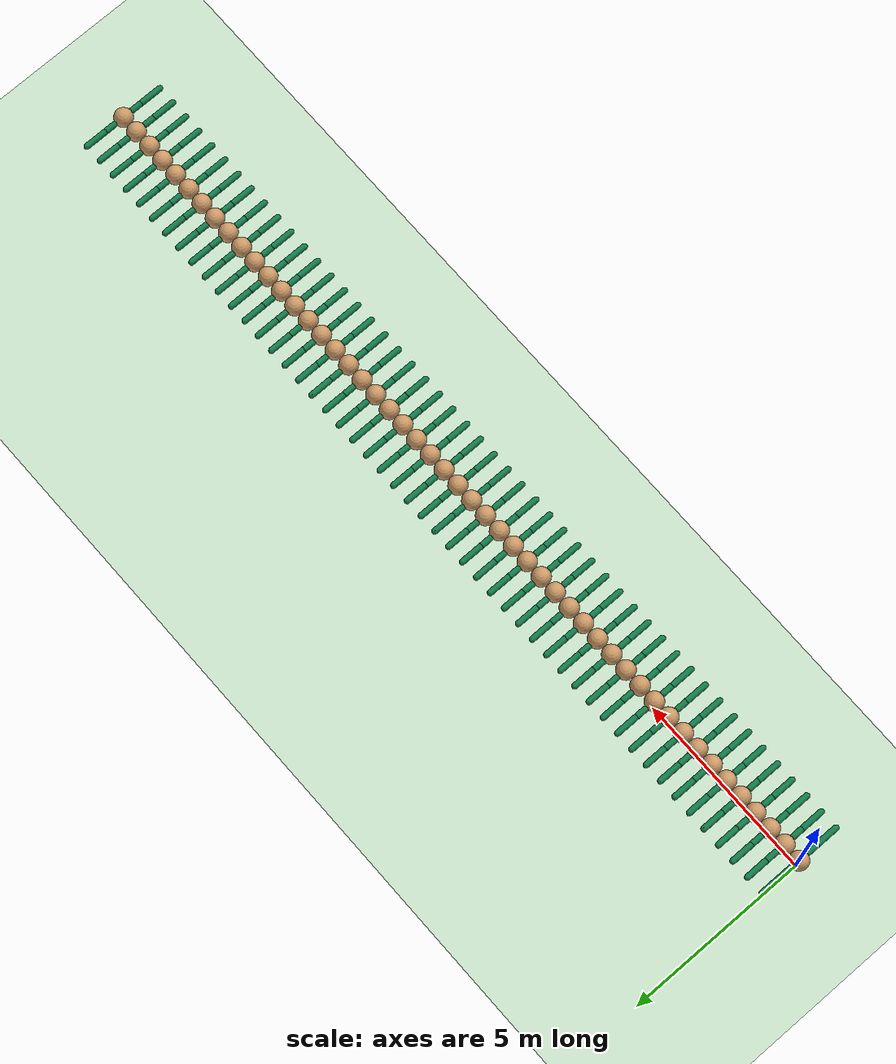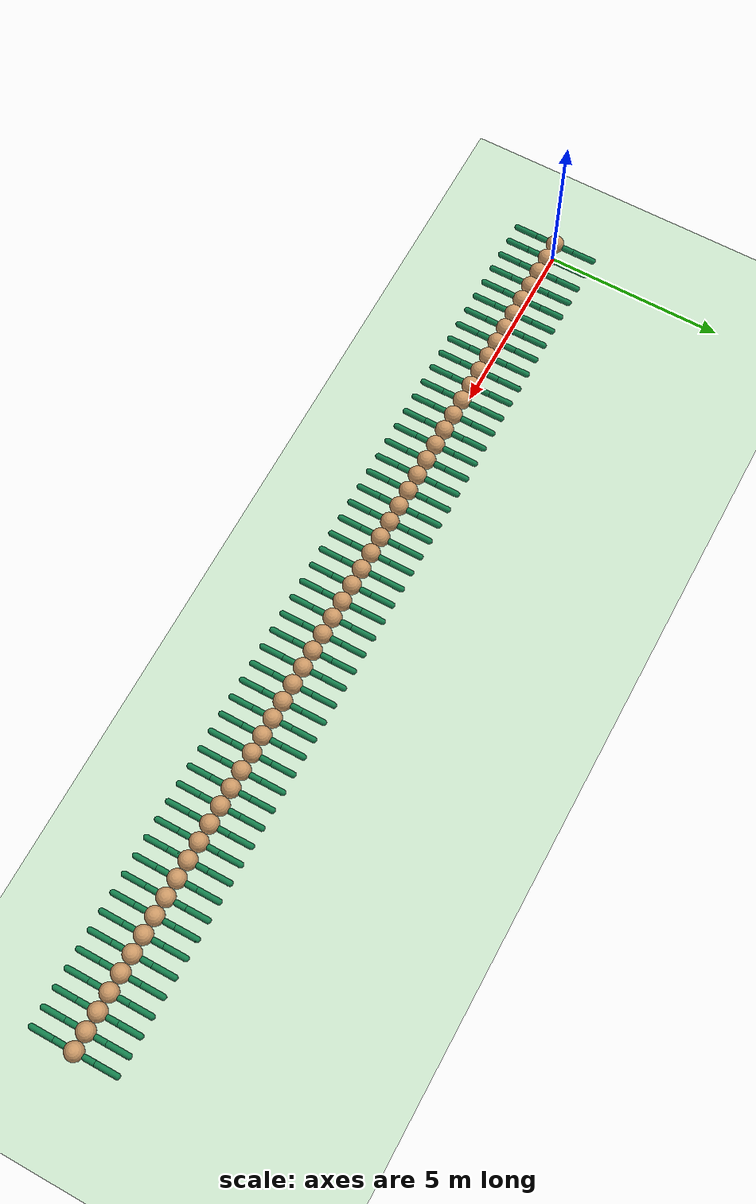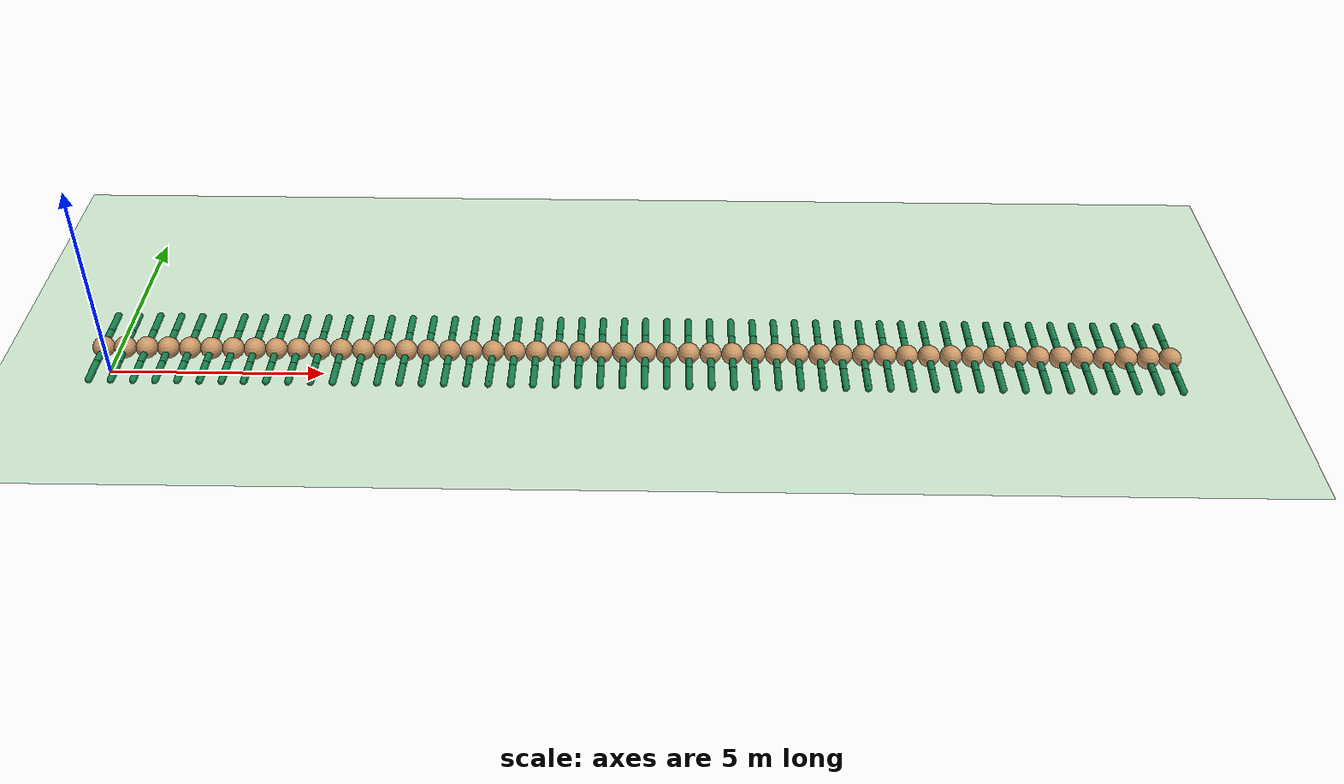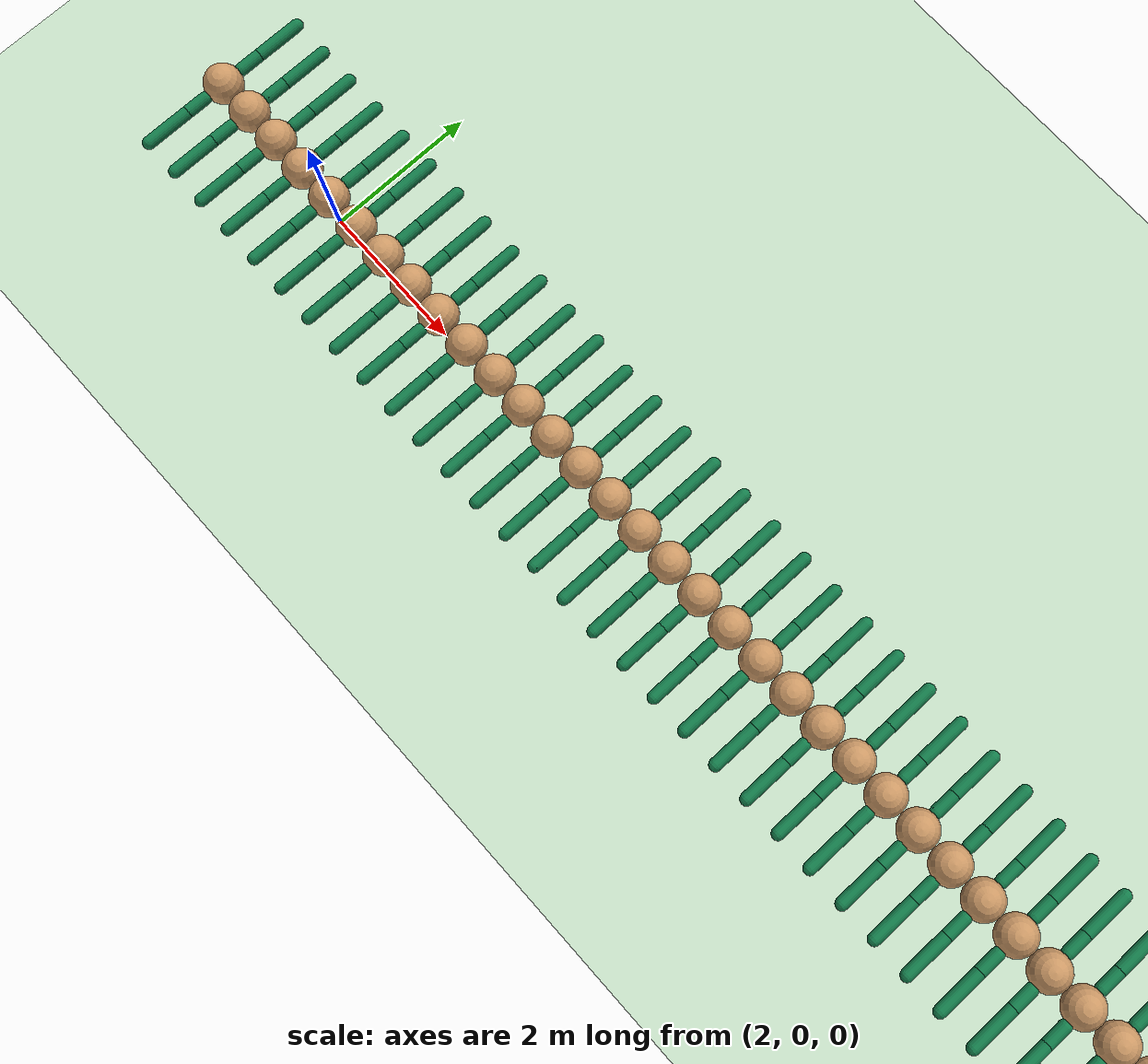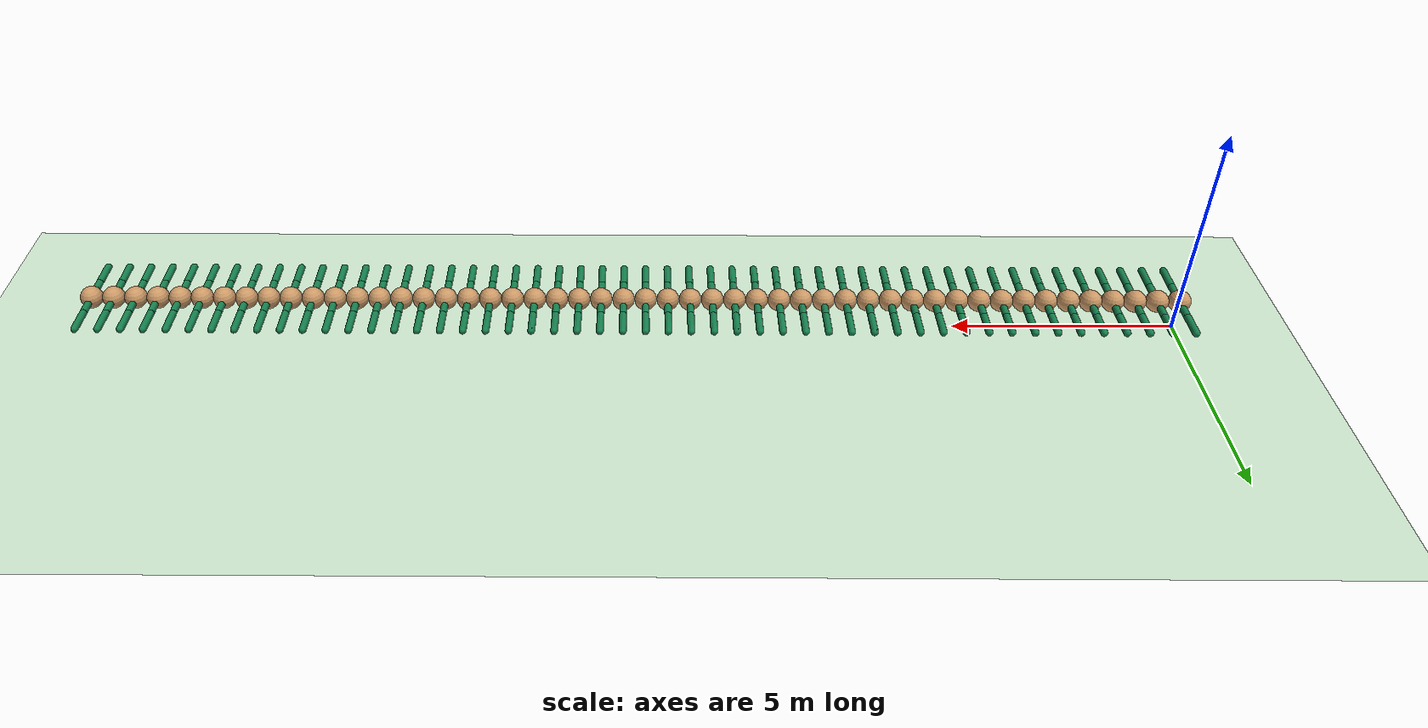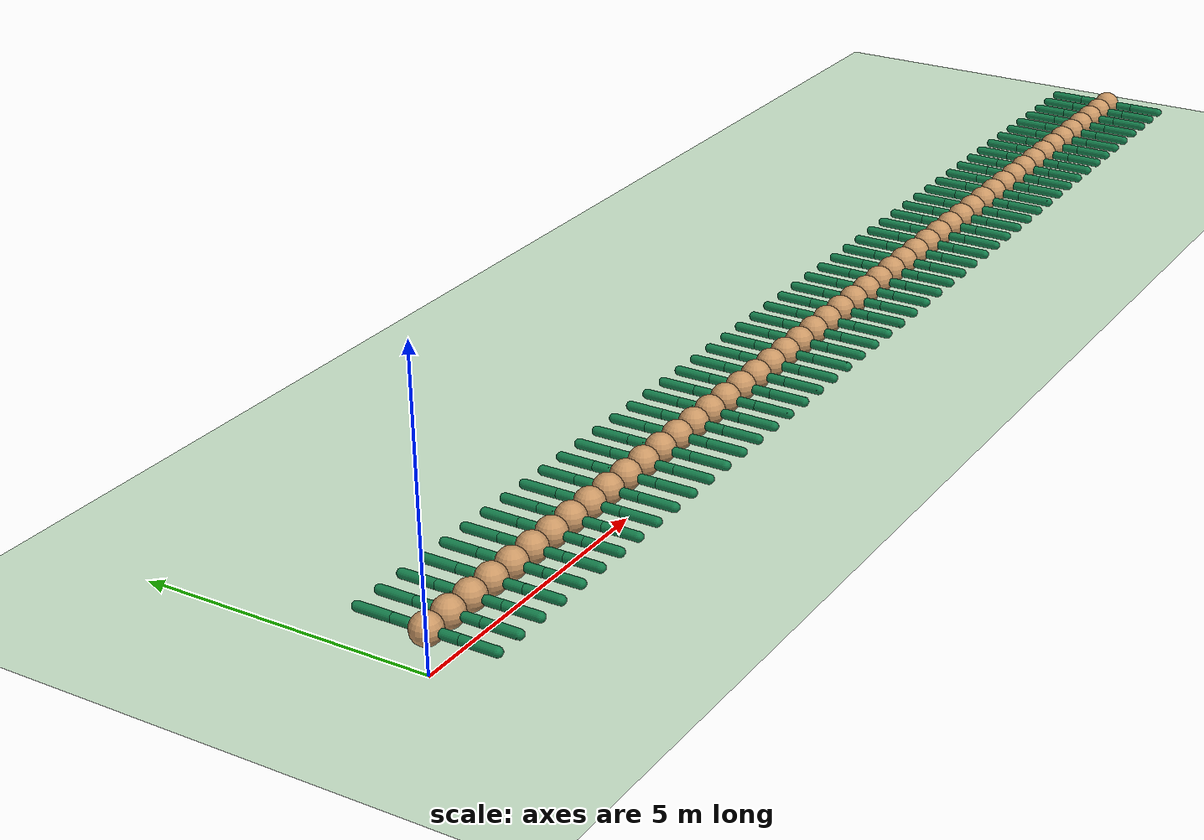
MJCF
<mujoco model="centipede">
  <compiler angle="degree" coordinate="local" inertiafromgeom="true"/>

  <option integrator="RK4" timestep="0.01"/>

  <default>
    <joint armature="1" damping="1" limited="true"/>
    <geom conaffinity="0" condim="3" density="25.0" friction="1.5 0.1 0.1" margin="0.01" rgba="0.8 0.6 0.4 1"/>
  </default>

  <asset>
    <texture builtin="gradient" height="100" rgb1="1 1 1" rgb2="0 0 0" type="skybox" width="100"/>
    <texture builtin="flat" height="1278" mark="cross" markrgb="1 1 1" name="texgeom" random="0.01" rgb1="0.8 0.6 0.4" rgb2="0.8 0.6 0.4" type="cube" width="127"/>
    <texture builtin="checker" height="100" name="texplane" rgb1="0 0 0" rgb2="0.8 0.8 0.8" type="2d" width="100"/>
    <material name="MatPlane" reflectance="0.5" shininess="1" specular="1" texrepeat="60 60" texture="texplane"/>
    <material name="geom" texture="texgeom" texuniform="true"/>
  </asset>

  <worldbody>
    <light cutoff="100" diffuse="1 1 1" dir="-0 0 -1.3" directional="true" exponent="1" pos="0 0 1.3" specular=".1 .1 .1"/>
    <geom conaffinity="1" condim="3" material="MatPlane" name="floor" pos="0 0 0" rgba="0.8 0.9 0.8 1" size="40 40 40" type="plane"/>
    <body name="torso_0" pos="0 0 0.75">
      <geom name="torsoGeom_0" pos="0 0 0" size="0.25" type="sphere" density="100"/>
      <joint armature="0" damping="0" limited="false" margin="0.01" name="root" pos="0 0 0" type="free"/>

      <body name="legbody_0" pos="0.0 -0.28 0">
        <joint axis="0 0 1" name="lefthip_0" pos="0.0 0.0 0.0" range="-40 40" type="hinge"/>
        <geom fromto="0.0 0.0 0.0 0.0 -0.28 0.0" name="legGeom_0" size="0.08" type="capsule" rgba=".08 .5 .3 1"/>
        <body pos="0 -0.28 0" name="frontFoot_0">
          <joint axis="1 0 0" name="ankle_0" pos="0.0 0.0 0.0" range="30 100" type="hinge"/>
          <geom fromto="0.0 0.0 0.0 0 -0.6 0.0" name="ankleGeom_0" size="0.08" type="capsule" rgba=".08 .5 .3 1"/>
        </body>
      </body>

      <body name="legbody_1" pos="0.0 0.28 0">
        <joint axis="0 0 1" name="righthip_1" pos="0.0 0.0 0.0" range="-40 40" type="hinge"/>
        <geom fromto="0.0 0.0 0.0 0.0 0.28 0.0" name="legGeom_1" size="0.08" type="capsule" rgba=".08 .5 .3 1"/>
        <body pos="0 0.28 0" name="frontFoot_1">
          <joint axis="-1 0 0" name="ankle_1" pos="0.0 0.0 0.0" range="30 100" type="hinge"/>
          <geom fromto="0.0 0.0 0.0 0 0.6 0.0" name="ankleGeom_1" size="0.08" type="capsule" rgba=".08 .5 .3 1"/>
        </body>
      </body>

      <body name="torso_1" pos="0.50 0 0">
        <geom name="torsoGeom_1" pos="0 0 0" size="0.25" type="sphere" density="100"/>
        <joint axis="0 0 1" name="body_1" pos="-0.25 0.0 0.0" range="-20 20" type="hinge"/>
        <joint axis="0 1 0" name="bodyupdown_1" pos="-0.25 0.0 0.0" range="-10 30" type="hinge"/>

        <body name="legbody_2" pos="0.0 -0.28 0">
          <joint axis="0 0 1" name="lefthip_2" pos="0.0 0.0 0.0" range="-40 40" type="hinge"/>
          <geom fromto="0.0 0.0 0.0 0.0 -0.28 0.0" name="legGeom_2" size="0.08" type="capsule" rgba=".08 .5 .3 1"/>
          <body pos="0 -0.28 0" name="frontFoot_2">
            <joint axis="1 0 0" name="ankle_2" pos="0.0 0.0 0.0" range="30 100" type="hinge"/>
            <geom fromto="0.0 0.0 0.0 0 -0.6 0.0" name="ankleGeom_2" size="0.08" type="capsule" rgba=".08 .5 .3 1"/>
          </body>
        </body>

        <body name="legbody_3" pos="0.0 0.28 0">
          <joint axis="0 0 1" name="righthip_3" pos="0.0 0.0 0.0" range="-40 40" type="hinge"/>
          <geom fromto="0.0 0.0 0.0 0.0 0.28 0.0" name="legGeom_3" size="0.08" type="capsule" rgba=".08 .5 .3 1"/>
          <body pos="0 0.28 0" name="frontFoot_3">
            <joint axis="-1 0 0" name="ankle_3" pos="0.0 0.0 0.0" range="30 100" type="hinge"/>
            <geom fromto="0.0 0.0 0.0 0 0.6 0.0" name="ankleGeom_3" size="0.08" type="capsule" rgba=".08 .5 .3 1"/>
          </body>
        </body>

        <body name="torso_2" pos="0.50 0 0">
          <geom name="torsoGeom_2" pos="0 0 0" size="0.25" type="sphere" density="100"/>
          <joint axis="0 0 1" name="body_2" pos="-0.25 0.0 0.0" range="-20 20" type="hinge"/>
          <joint axis="0 1 0" name="bodyupdown_2" pos="-0.25 0.0 0.0" range="-10 30" type="hinge"/>

          <body name="legbody_4" pos="0.0 -0.28 0">
            <joint axis="0 0 1" name="lefthip_4" pos="0.0 0.0 0.0" range="-40 40" type="hinge"/>
            <geom fromto="0.0 0.0 0.0 0.0 -0.28 0.0" name="legGeom_4" size="0.08" type="capsule" rgba=".08 .5 .3 1"/>
            <body pos="0 -0.28 0" name="frontFoot_4">
              <joint axis="1 0 0" name="ankle_4" pos="0.0 0.0 0.0" range="30 100" type="hinge"/>
              <geom fromto="0.0 0.0 0.0 0 -0.6 0.0" name="ankleGeom_4" size="0.08" type="capsule" rgba=".08 .5 .3 1"/>
            </body>
          </body>

          <body name="legbody_5" pos="0.0 0.28 0">
            <joint axis="0 0 1" name="righthip_5" pos="0.0 0.0 0.0" range="-40 40" type="hinge"/>
            <geom fromto="0.0 0.0 0.0 0.0 0.28 0.0" name="legGeom_5" size="0.08" type="capsule" rgba=".08 .5 .3 1"/>
            <body pos="0 0.28 0" name="frontFoot_5">
              <joint axis="-1 0 0" name="ankle_5" pos="0.0 0.0 0.0" range="30 100" type="hinge"/>
              <geom fromto="0.0 0.0 0.0 0 0.6 0.0" name="ankleGeom_5" size="0.08" type="capsule" rgba=".08 .5 .3 1"/>
            </body>
          </body>

          <body name="torso_3" pos="0.50 0 0">
            <geom name="torsoGeom_3" pos="0 0 0" size="0.25" type="sphere" density="100"/>
            <joint axis="0 0 1" name="body_3" pos="-0.25 0.0 0.0" range="-20 20" type="hinge"/>
            <joint axis="0 1 0" name="bodyupdown_3" pos="-0.25 0.0 0.0" range="-10 30" type="hinge"/>

            <body name="legbody_6" pos="0.0 -0.28 0">
              <joint axis="0 0 1" name="lefthip_6" pos="0.0 0.0 0.0" range="-40 40" type="hinge"/>
              <geom fromto="0.0 0.0 0.0 0.0 -0.28 0.0" name="legGeom_6" size="0.08" type="capsule" rgba=".08 .5 .3 1"/>
              <body pos="0 -0.28 0" name="frontFoot_6">
                <joint axis="1 0 0" name="ankle_6" pos="0.0 0.0 0.0" range="30 100" type="hinge"/>
                <geom fromto="0.0 0.0 0.0 0 -0.6 0.0" name="ankleGeom_6" size="0.08" type="capsule" rgba=".08 .5 .3 1"/>
              </body>
            </body>

            <body name="legbody_7" pos="0.0 0.28 0">
              <joint axis="0 0 1" name="righthip_7" pos="0.0 0.0 0.0" range="-40 40" type="hinge"/>
              <geom fromto="0.0 0.0 0.0 0.0 0.28 0.0" name="legGeom_7" size="0.08" type="capsule" rgba=".08 .5 .3 1"/>
              <body pos="0 0.28 0" name="frontFoot_7">
                <joint axis="-1 0 0" name="ankle_7" pos="0.0 0.0 0.0" range="30 100" type="hinge"/>
                <geom fromto="0.0 0.0 0.0 0 0.6 0.0" name="ankleGeom_7" size="0.08" type="capsule" rgba=".08 .5 .3 1"/>
              </body>
            </body>

            <body name="torso_4" pos="0.50 0 0">
              <geom name="torsoGeom_4" pos="0 0 0" size="0.25" type="sphere" density="100"/>
              <joint axis="0 0 1" name="body_4" pos="-0.25 0.0 0.0" range="-20 20" type="hinge"/>
              <joint axis="0 1 0" name="bodyupdown_4" pos="-0.25 0.0 0.0" range="-10 30" type="hinge"/>

              <body name="legbody_8" pos="0.0 -0.28 0">
                <joint axis="0 0 1" name="lefthip_8" pos="0.0 0.0 0.0" range="-40 40" type="hinge"/>
                <geom fromto="0.0 0.0 0.0 0.0 -0.28 0.0" name="legGeom_8" size="0.08" type="capsule" rgba=".08 .5 .3 1"/>
                <body pos="0 -0.28 0" name="frontFoot_8">
                  <joint axis="1 0 0" name="ankle_8" pos="0.0 0.0 0.0" range="30 100" type="hinge"/>
                  <geom fromto="0.0 0.0 0.0 0 -0.6 0.0" name="ankleGeom_8" size="0.08" type="capsule" rgba=".08 .5 .3 1"/>
                </body>
              </body>

              <body name="legbody_9" pos="0.0 0.28 0">
                <joint axis="0 0 1" name="righthip_9" pos="0.0 0.0 0.0" range="-40 40" type="hinge"/>
                <geom fromto="0.0 0.0 0.0 0.0 0.28 0.0" name="legGeom_9" size="0.08" type="capsule" rgba=".08 .5 .3 1"/>
                <body pos="0 0.28 0" name="frontFoot_9">
                  <joint axis="-1 0 0" name="ankle_9" pos="0.0 0.0 0.0" range="30 100" type="hinge"/>
                  <geom fromto="0.0 0.0 0.0 0 0.6 0.0" name="ankleGeom_9" size="0.08" type="capsule" rgba=".08 .5 .3 1"/>
                </body>
              </body>

              <body name="torso_5" pos="0.50 0 0">
                <geom name="torsoGeom_5" pos="0 0 0" size="0.25" type="sphere" density="100"/>
                <joint axis="0 0 1" name="body_5" pos="-0.25 0.0 0.0" range="-20 20" type="hinge"/>
                <joint axis="0 1 0" name="bodyupdown_5" pos="-0.25 0.0 0.0" range="-10 30" type="hinge"/>

                <body name="legbody_10" pos="0.0 -0.28 0">
                  <joint axis="0 0 1" name="lefthip_10" pos="0.0 0.0 0.0" range="-40 40" type="hinge"/>
                  <geom fromto="0.0 0.0 0.0 0.0 -0.28 0.0" name="legGeom_10" size="0.08" type="capsule" rgba=".08 .5 .3 1"/>
                  <body pos="0 -0.28 0" name="frontFoot_10">
                    <joint axis="1 0 0" name="ankle_10" pos="0.0 0.0 0.0" range="30 100" type="hinge"/>
                    <geom fromto="0.0 0.0 0.0 0 -0.6 0.0" name="ankleGeom_10" size="0.08" type="capsule" rgba=".08 .5 .3 1"/>
                  </body>
                </body>

                <body name="legbody_11" pos="0.0 0.28 0">
                  <joint axis="0 0 1" name="righthip_11" pos="0.0 0.0 0.0" range="-40 40" type="hinge"/>
                  <geom fromto="0.0 0.0 0.0 0.0 0.28 0.0" name="legGeom_11" size="0.08" type="capsule" rgba=".08 .5 .3 1"/>
                  <body pos="0 0.28 0" name="frontFoot_11">
                    <joint axis="-1 0 0" name="ankle_11" pos="0.0 0.0 0.0" range="30 100" type="hinge"/>
                    <geom fromto="0.0 0.0 0.0 0 0.6 0.0" name="ankleGeom_11" size="0.08" type="capsule" rgba=".08 .5 .3 1"/>
                  </body>
                </body>

                <body name="torso_6" pos="0.50 0 0">
                  <geom name="torsoGeom_6" pos="0 0 0" size="0.25" type="sphere" density="100"/>
                  <joint axis="0 0 1" name="body_6" pos="-0.25 0.0 0.0" range="-20 20" type="hinge"/>
                  <joint axis="0 1 0" name="bodyupdown_6" pos="-0.25 0.0 0.0" range="-10 30" type="hinge"/>

                  <body name="legbody_12" pos="0.0 -0.28 0">
                    <joint axis="0 0 1" name="lefthip_12" pos="0.0 0.0 0.0" range="-40 40" type="hinge"/>
                    <geom fromto="0.0 0.0 0.0 0.0 -0.28 0.0" name="legGeom_12" size="0.08" type="capsule" rgba=".08 .5 .3 1"/>
                    <body pos="0 -0.28 0" name="frontFoot_12">
                      <joint axis="1 0 0" name="ankle_12" pos="0.0 0.0 0.0" range="30 100" type="hinge"/>
                      <geom fromto="0.0 0.0 0.0 0 -0.6 0.0" name="ankleGeom_12" size="0.08" type="capsule" rgba=".08 .5 .3 1"/>
                    </body>
                  </body>

                  <body name="legbody_13" pos="0.0 0.28 0">
                    <joint axis="0 0 1" name="righthip_13" pos="0.0 0.0 0.0" range="-40 40" type="hinge"/>
                    <geom fromto="0.0 0.0 0.0 0.0 0.28 0.0" name="legGeom_13" size="0.08" type="capsule" rgba=".08 .5 .3 1"/>
                    <body pos="0 0.28 0" name="frontFoot_13">
                      <joint axis="-1 0 0" name="ankle_13" pos="0.0 0.0 0.0" range="30 100" type="hinge"/>
                      <geom fromto="0.0 0.0 0.0 0 0.6 0.0" name="ankleGeom_13" size="0.08" type="capsule" rgba=".08 .5 .3 1"/>
                    </body>
                  </body>

                  <body name="torso_7" pos="0.50 0 0">
                    <geom name="torsoGeom_7" pos="0 0 0" size="0.25" type="sphere" density="100"/>
                    <joint axis="0 0 1" name="body_7" pos="-0.25 0.0 0.0" range="-20 20" type="hinge"/>
                    <joint axis="0 1 0" name="bodyupdown_7" pos="-0.25 0.0 0.0" range="-10 30" type="hinge"/>

                    <body name="legbody_14" pos="0.0 -0.28 0">
                      <joint axis="0 0 1" name="lefthip_14" pos="0.0 0.0 0.0" range="-40 40" type="hinge"/>
                      <geom fromto="0.0 0.0 0.0 0.0 -0.28 0.0" name="legGeom_14" size="0.08" type="capsule" rgba=".08 .5 .3 1"/>
                      <body pos="0 -0.28 0" name="frontFoot_14">
                        <joint axis="1 0 0" name="ankle_14" pos="0.0 0.0 0.0" range="30 100" type="hinge"/>
                        <geom fromto="0.0 0.0 0.0 0 -0.6 0.0" name="ankleGeom_14" size="0.08" type="capsule" rgba=".08 .5 .3 1"/>
                      </body>
                    </body>

                    <body name="legbody_15" pos="0.0 0.28 0">
                      <joint axis="0 0 1" name="righthip_15" pos="0.0 0.0 0.0" range="-40 40" type="hinge"/>
                      <geom fromto="0.0 0.0 0.0 0.0 0.28 0.0" name="legGeom_15" size="0.08" type="capsule" rgba=".08 .5 .3 1"/>
                      <body pos="0 0.28 0" name="frontFoot_15">
                        <joint axis="-1 0 0" name="ankle_15" pos="0.0 0.0 0.0" range="30 100" type="hinge"/>
                        <geom fromto="0.0 0.0 0.0 0 0.6 0.0" name="ankleGeom_15" size="0.08" type="capsule" rgba=".08 .5 .3 1"/>
                      </body>
                    </body>

                    <body name="torso_8" pos="0.50 0 0">
                      <geom name="torsoGeom_8" pos="0 0 0" size="0.25" type="sphere" density="100"/>
                      <joint axis="0 0 1" name="body_8" pos="-0.25 0.0 0.0" range="-20 20" type="hinge"/>
                      <joint axis="0 1 0" name="bodyupdown_8" pos="-0.25 0.0 0.0" range="-10 30" type="hinge"/>

                      <body name="legbody_16" pos="0.0 -0.28 0">
                        <joint axis="0 0 1" name="lefthip_16" pos="0.0 0.0 0.0" range="-40 40" type="hinge"/>
                        <geom fromto="0.0 0.0 0.0 0.0 -0.28 0.0" name="legGeom_16" size="0.08" type="capsule" rgba=".08 .5 .3 1"/>
                        <body pos="0 -0.28 0" name="frontFoot_16">
                          <joint axis="1 0 0" name="ankle_16" pos="0.0 0.0 0.0" range="30 100" type="hinge"/>
                          <geom fromto="0.0 0.0 0.0 0 -0.6 0.0" name="ankleGeom_16" size="0.08" type="capsule" rgba=".08 .5 .3 1"/>
                        </body>
                      </body>

                      <body name="legbody_17" pos="0.0 0.28 0">
                        <joint axis="0 0 1" name="righthip_17" pos="0.0 0.0 0.0" range="-40 40" type="hinge"/>
                        <geom fromto="0.0 0.0 0.0 0.0 0.28 0.0" name="legGeom_17" size="0.08" type="capsule" rgba=".08 .5 .3 1"/>
                        <body pos="0 0.28 0" name="frontFoot_17">
                          <joint axis="-1 0 0" name="ankle_17" pos="0.0 0.0 0.0" range="30 100" type="hinge"/>
                          <geom fromto="0.0 0.0 0.0 0 0.6 0.0" name="ankleGeom_17" size="0.08" type="capsule" rgba=".08 .5 .3 1"/>
                        </body>
                      </body>

                      <body name="torso_9" pos="0.50 0 0">
                        <geom name="torsoGeom_9" pos="0 0 0" size="0.25" type="sphere" density="100"/>
                        <joint axis="0 0 1" name="body_9" pos="-0.25 0.0 0.0" range="-20 20" type="hinge"/>
                        <joint axis="0 1 0" name="bodyupdown_9" pos="-0.25 0.0 0.0" range="-10 30" type="hinge"/>

                        <body name="legbody_18" pos="0.0 -0.28 0">
                          <joint axis="0 0 1" name="lefthip_18" pos="0.0 0.0 0.0" range="-40 40" type="hinge"/>
                          <geom fromto="0.0 0.0 0.0 0.0 -0.28 0.0" name="legGeom_18" size="0.08" type="capsule" rgba=".08 .5 .3 1"/>
                          <body pos="0 -0.28 0" name="frontFoot_18">
                            <joint axis="1 0 0" name="ankle_18" pos="0.0 0.0 0.0" range="30 100" type="hinge"/>
                            <geom fromto="0.0 0.0 0.0 0 -0.6 0.0" name="ankleGeom_18" size="0.08" type="capsule" rgba=".08 .5 .3 1"/>
                          </body>
                        </body>

                        <body name="legbody_19" pos="0.0 0.28 0">
                          <joint axis="0 0 1" name="righthip_19" pos="0.0 0.0 0.0" range="-40 40" type="hinge"/>
                          <geom fromto="0.0 0.0 0.0 0.0 0.28 0.0" name="legGeom_19" size="0.08" type="capsule" rgba=".08 .5 .3 1"/>
                          <body pos="0 0.28 0" name="frontFoot_19">
                            <joint axis="-1 0 0" name="ankle_19" pos="0.0 0.0 0.0" range="30 100" type="hinge"/>
                            <geom fromto="0.0 0.0 0.0 0 0.6 0.0" name="ankleGeom_19" size="0.08" type="capsule" rgba=".08 .5 .3 1"/>
                          </body>
                        </body>

                        <body name="torso_10" pos="0.50 0 0">
                          <geom name="torsoGeom_10" pos="0 0 0" size="0.25" type="sphere" density="100"/>
                          <joint axis="0 0 1" name="body_10" pos="-0.25 0.0 0.0" range="-20 20" type="hinge"/>
                          <joint axis="0 1 0" name="bodyupdown_10" pos="-0.25 0.0 0.0" range="-10 30" type="hinge"/>

                          <body name="legbody_20" pos="0.0 -0.28 0">
                            <joint axis="0 0 1" name="lefthip_20" pos="0.0 0.0 0.0" range="-40 40" type="hinge"/>
                            <geom fromto="0.0 0.0 0.0 0.0 -0.28 0.0" name="legGeom_20" size="0.08" type="capsule" rgba=".08 .5 .3 1"/>
                            <body pos="0 -0.28 0" name="frontFoot_20">
                              <joint axis="1 0 0" name="ankle_20" pos="0.0 0.0 0.0" range="30 100" type="hinge"/>
                              <geom fromto="0.0 0.0 0.0 0 -0.6 0.0" name="ankleGeom_20" size="0.08" type="capsule" rgba=".08 .5 .3 1"/>
                            </body>
                          </body>

                          <body name="legbody_21" pos="0.0 0.28 0">
                            <joint axis="0 0 1" name="righthip_21" pos="0.0 0.0 0.0" range="-40 40" type="hinge"/>
                            <geom fromto="0.0 0.0 0.0 0.0 0.28 0.0" name="legGeom_21" size="0.08" type="capsule" rgba=".08 .5 .3 1"/>
                            <body pos="0 0.28 0" name="frontFoot_21">
                              <joint axis="-1 0 0" name="ankle_21" pos="0.0 0.0 0.0" range="30 100" type="hinge"/>
                              <geom fromto="0.0 0.0 0.0 0 0.6 0.0" name="ankleGeom_21" size="0.08" type="capsule" rgba=".08 .5 .3 1"/>
                            </body>
                          </body>

                          <body name="torso_11" pos="0.50 0 0">
                            <geom name="torsoGeom_11" pos="0 0 0" size="0.25" type="sphere" density="100"/>
                            <joint axis="0 0 1" name="body_11" pos="-0.25 0.0 0.0" range="-20 20" type="hinge"/>
                            <joint axis="0 1 0" name="bodyupdown_11" pos="-0.25 0.0 0.0" range="-10 30" type="hinge"/>

                            <body name="legbody_22" pos="0.0 -0.28 0">
                              <joint axis="0 0 1" name="lefthip_22" pos="0.0 0.0 0.0" range="-40 40" type="hinge"/>
                              <geom fromto="0.0 0.0 0.0 0.0 -0.28 0.0" name="legGeom_22" size="0.08" type="capsule" rgba=".08 .5 .3 1"/>
                              <body pos="0 -0.28 0" name="frontFoot_22">
                                <joint axis="1 0 0" name="ankle_22" pos="0.0 0.0 0.0" range="30 100" type="hinge"/>
                                <geom fromto="0.0 0.0 0.0 0 -0.6 0.0" name="ankleGeom_22" size="0.08" type="capsule" rgba=".08 .5 .3 1"/>
                              </body>
                            </body>

                            <body name="legbody_23" pos="0.0 0.28 0">
                              <joint axis="0 0 1" name="righthip_23" pos="0.0 0.0 0.0" range="-40 40" type="hinge"/>
                              <geom fromto="0.0 0.0 0.0 0.0 0.28 0.0" name="legGeom_23" size="0.08" type="capsule" rgba=".08 .5 .3 1"/>
                              <body pos="0 0.28 0" name="frontFoot_23">
                                <joint axis="-1 0 0" name="ankle_23" pos="0.0 0.0 0.0" range="30 100" type="hinge"/>
                                <geom fromto="0.0 0.0 0.0 0 0.6 0.0" name="ankleGeom_23" size="0.08" type="capsule" rgba=".08 .5 .3 1"/>
                              </body>
                            </body>

                            <body name="torso_12" pos="0.50 0 0">
                              <geom name="torsoGeom_12" pos="0 0 0" size="0.25" type="sphere" density="100"/>
                              <joint axis="0 0 1" name="body_12" pos="-0.25 0.0 0.0" range="-20 20" type="hinge"/>
                              <joint axis="0 1 0" name="bodyupdown_12" pos="-0.25 0.0 0.0" range="-10 30" type="hinge"/>

                              <body name="legbody_24" pos="0.0 -0.28 0">
                                <joint axis="0 0 1" name="lefthip_24" pos="0.0 0.0 0.0" range="-40 40" type="hinge"/>
                                <geom fromto="0.0 0.0 0.0 0.0 -0.28 0.0" name="legGeom_24" size="0.08" type="capsule" rgba=".08 .5 .3 1"/>
                                <body pos="0 -0.28 0" name="frontFoot_24">
                                  <joint axis="1 0 0" name="ankle_24" pos="0.0 0.0 0.0" range="30 100" type="hinge"/>
                                  <geom fromto="0.0 0.0 0.0 0 -0.6 0.0" name="ankleGeom_24" size="0.08" type="capsule" rgba=".08 .5 .3 1"/>
                                </body>
                              </body>

                              <body name="legbody_25" pos="0.0 0.28 0">
                                <joint axis="0 0 1" name="righthip_25" pos="0.0 0.0 0.0" range="-40 40" type="hinge"/>
                                <geom fromto="0.0 0.0 0.0 0.0 0.28 0.0" name="legGeom_25" size="0.08" type="capsule" rgba=".08 .5 .3 1"/>
                                <body pos="0 0.28 0" name="frontFoot_25">
                                  <joint axis="-1 0 0" name="ankle_25" pos="0.0 0.0 0.0" range="30 100" type="hinge"/>
                                  <geom fromto="0.0 0.0 0.0 0 0.6 0.0" name="ankleGeom_25" size="0.08" type="capsule" rgba=".08 .5 .3 1"/>
                                </body>
                              </body>

                              <body name="torso_13" pos="0.50 0 0">
                                <geom name="torsoGeom_13" pos="0 0 0" size="0.25" type="sphere" density="100"/>
                                <joint axis="0 0 1" name="body_13" pos="-0.25 0.0 0.0" range="-20 20" type="hinge"/>
                                <joint axis="0 1 0" name="bodyupdown_13" pos="-0.25 0.0 0.0" range="-10 30" type="hinge"/>

                                <body name="legbody_26" pos="0.0 -0.28 0">
                                  <joint axis="0 0 1" name="lefthip_26" pos="0.0 0.0 0.0" range="-40 40" type="hinge"/>
                                  <geom fromto="0.0 0.0 0.0 0.0 -0.28 0.0" name="legGeom_26" size="0.08" type="capsule" rgba=".08 .5 .3 1"/>
                                  <body pos="0 -0.28 0" name="frontFoot_26">
                                    <joint axis="1 0 0" name="ankle_26" pos="0.0 0.0 0.0" range="30 100" type="hinge"/>
                                    <geom fromto="0.0 0.0 0.0 0 -0.6 0.0" name="ankleGeom_26" size="0.08" type="capsule" rgba=".08 .5 .3 1"/>
                                  </body>
                                </body>

                                <body name="legbody_27" pos="0.0 0.28 0">
                                  <joint axis="0 0 1" name="righthip_27" pos="0.0 0.0 0.0" range="-40 40" type="hinge"/>
                                  <geom fromto="0.0 0.0 0.0 0.0 0.28 0.0" name="legGeom_27" size="0.08" type="capsule" rgba=".08 .5 .3 1"/>
                                  <body pos="0 0.28 0" name="frontFoot_27">
                                    <joint axis="-1 0 0" name="ankle_27" pos="0.0 0.0 0.0" range="30 100" type="hinge"/>
                                    <geom fromto="0.0 0.0 0.0 0 0.6 0.0" name="ankleGeom_27" size="0.08" type="capsule" rgba=".08 .5 .3 1"/>
                                  </body>
                                </body>

                                <body name="torso_14" pos="0.50 0 0">
                                  <geom name="torsoGeom_14" pos="0 0 0" size="0.25" type="sphere" density="100"/>
                                  <joint axis="0 0 1" name="body_14" pos="-0.25 0.0 0.0" range="-20 20" type="hinge"/>
                                  <joint axis="0 1 0" name="bodyupdown_14" pos="-0.25 0.0 0.0" range="-10 30" type="hinge"/>

                                  <body name="legbody_28" pos="0.0 -0.28 0">
                                    <joint axis="0 0 1" name="lefthip_28" pos="0.0 0.0 0.0" range="-40 40" type="hinge"/>
                                    <geom fromto="0.0 0.0 0.0 0.0 -0.28 0.0" name="legGeom_28" size="0.08" type="capsule" rgba=".08 .5 .3 1"/>
                                    <body pos="0 -0.28 0" name="frontFoot_28">
                                      <joint axis="1 0 0" name="ankle_28" pos="0.0 0.0 0.0" range="30 100" type="hinge"/>
                                      <geom fromto="0.0 0.0 0.0 0 -0.6 0.0" name="ankleGeom_28" size="0.08" type="capsule" rgba=".08 .5 .3 1"/>
                                    </body>
                                  </body>

                                  <body name="legbody_29" pos="0.0 0.28 0">
                                    <joint axis="0 0 1" name="righthip_29" pos="0.0 0.0 0.0" range="-40 40" type="hinge"/>
                                    <geom fromto="0.0 0.0 0.0 0.0 0.28 0.0" name="legGeom_29" size="0.08" type="capsule" rgba=".08 .5 .3 1"/>
                                    <body pos="0 0.28 0" name="frontFoot_29">
                                      <joint axis="-1 0 0" name="ankle_29" pos="0.0 0.0 0.0" range="30 100" type="hinge"/>
                                      <geom fromto="0.0 0.0 0.0 0 0.6 0.0" name="ankleGeom_29" size="0.08" type="capsule" rgba=".08 .5 .3 1"/>
                                    </body>
                                  </body>

                                  <body name="torso_15" pos="0.50 0 0">
                                    <geom name="torsoGeom_15" pos="0 0 0" size="0.25" type="sphere" density="100"/>
                                    <joint axis="0 0 1" name="body_15" pos="-0.25 0.0 0.0" range="-20 20" type="hinge"/>
                                    <joint axis="0 1 0" name="bodyupdown_15" pos="-0.25 0.0 0.0" range="-10 30" type="hinge"/>

                                    <body name="legbody_30" pos="0.0 -0.28 0">
                                      <joint axis="0 0 1" name="lefthip_30" pos="0.0 0.0 0.0" range="-40 40" type="hinge"/>
                                      <geom fromto="0.0 0.0 0.0 0.0 -0.28 0.0" name="legGeom_30" size="0.08" type="capsule" rgba=".08 .5 .3 1"/>
                                      <body pos="0 -0.28 0" name="frontFoot_30">
                                        <joint axis="1 0 0" name="ankle_30" pos="0.0 0.0 0.0" range="30 100" type="hinge"/>
                                        <geom fromto="0.0 0.0 0.0 0 -0.6 0.0" name="ankleGeom_30" size="0.08" type="capsule" rgba=".08 .5 .3 1"/>
                                      </body>
                                    </body>

                                    <body name="legbody_31" pos="0.0 0.28 0">
                                      <joint axis="0 0 1" name="righthip_31" pos="0.0 0.0 0.0" range="-40 40" type="hinge"/>
                                      <geom fromto="0.0 0.0 0.0 0.0 0.28 0.0" name="legGeom_31" size="0.08" type="capsule" rgba=".08 .5 .3 1"/>
                                      <body pos="0 0.28 0" name="frontFoot_31">
                                        <joint axis="-1 0 0" name="ankle_31" pos="0.0 0.0 0.0" range="30 100" type="hinge"/>
                                        <geom fromto="0.0 0.0 0.0 0 0.6 0.0" name="ankleGeom_31" size="0.08" type="capsule" rgba=".08 .5 .3 1"/>
                                      </body>
                                    </body>

                                    <body name="torso_16" pos="0.50 0 0">
                                      <geom name="torsoGeom_16" pos="0 0 0" size="0.25" type="sphere" density="100"/>
                                      <joint axis="0 0 1" name="body_16" pos="-0.25 0.0 0.0" range="-20 20" type="hinge"/>
                                      <joint axis="0 1 0" name="bodyupdown_16" pos="-0.25 0.0 0.0" range="-10 30" type="hinge"/>

                                      <body name="legbody_32" pos="0.0 -0.28 0">
                                        <joint axis="0 0 1" name="lefthip_32" pos="0.0 0.0 0.0" range="-40 40" type="hinge"/>
                                        <geom fromto="0.0 0.0 0.0 0.0 -0.28 0.0" name="legGeom_32" size="0.08" type="capsule" rgba=".08 .5 .3 1"/>
                                        <body pos="0 -0.28 0" name="frontFoot_32">
                                          <joint axis="1 0 0" name="ankle_32" pos="0.0 0.0 0.0" range="30 100" type="hinge"/>
                                          <geom fromto="0.0 0.0 0.0 0 -0.6 0.0" name="ankleGeom_32" size="0.08" type="capsule" rgba=".08 .5 .3 1"/>
                                        </body>
                                      </body>

                                      <body name="legbody_33" pos="0.0 0.28 0">
                                        <joint axis="0 0 1" name="righthip_33" pos="0.0 0.0 0.0" range="-40 40" type="hinge"/>
                                        <geom fromto="0.0 0.0 0.0 0.0 0.28 0.0" name="legGeom_33" size="0.08" type="capsule" rgba=".08 .5 .3 1"/>
                                        <body pos="0 0.28 0" name="frontFoot_33">
                                          <joint axis="-1 0 0" name="ankle_33" pos="0.0 0.0 0.0" range="30 100" type="hinge"/>
                                          <geom fromto="0.0 0.0 0.0 0 0.6 0.0" name="ankleGeom_33" size="0.08" type="capsule" rgba=".08 .5 .3 1"/>
                                        </body>
                                      </body>

                                      <body name="torso_17" pos="0.50 0 0">
                                        <geom name="torsoGeom_17" pos="0 0 0" size="0.25" type="sphere" density="100"/>
                                        <joint axis="0 0 1" name="body_17" pos="-0.25 0.0 0.0" range="-20 20" type="hinge"/>
                                        <joint axis="0 1 0" name="bodyupdown_17" pos="-0.25 0.0 0.0" range="-10 30" type="hinge"/>

                                        <body name="legbody_34" pos="0.0 -0.28 0">
                                          <joint axis="0 0 1" name="lefthip_34" pos="0.0 0.0 0.0" range="-40 40" type="hinge"/>
                                          <geom fromto="0.0 0.0 0.0 0.0 -0.28 0.0" name="legGeom_34" size="0.08" type="capsule" rgba=".08 .5 .3 1"/>
                                          <body pos="0 -0.28 0" name="frontFoot_34">
                                            <joint axis="1 0 0" name="ankle_34" pos="0.0 0.0 0.0" range="30 100" type="hinge"/>
                                            <geom fromto="0.0 0.0 0.0 0 -0.6 0.0" name="ankleGeom_34" size="0.08" type="capsule" rgba=".08 .5 .3 1"/>
                                          </body>
                                        </body>

                                        <body name="legbody_35" pos="0.0 0.28 0">
                                          <joint axis="0 0 1" name="righthip_35" pos="0.0 0.0 0.0" range="-40 40" type="hinge"/>
                                          <geom fromto="0.0 0.0 0.0 0.0 0.28 0.0" name="legGeom_35" size="0.08" type="capsule" rgba=".08 .5 .3 1"/>
                                          <body pos="0 0.28 0" name="frontFoot_35">
                                            <joint axis="-1 0 0" name="ankle_35" pos="0.0 0.0 0.0" range="30 100" type="hinge"/>
                                            <geom fromto="0.0 0.0 0.0 0 0.6 0.0" name="ankleGeom_35" size="0.08" type="capsule" rgba=".08 .5 .3 1"/>
                                          </body>
                                        </body>

                                        <body name="torso_18" pos="0.50 0 0">
                                          <geom name="torsoGeom_18" pos="0 0 0" size="0.25" type="sphere" density="100"/>
                                          <joint axis="0 0 1" name="body_18" pos="-0.25 0.0 0.0" range="-20 20" type="hinge"/>
                                          <joint axis="0 1 0" name="bodyupdown_18" pos="-0.25 0.0 0.0" range="-10 30" type="hinge"/>

                                          <body name="legbody_36" pos="0.0 -0.28 0">
                                            <joint axis="0 0 1" name="lefthip_36" pos="0.0 0.0 0.0" range="-40 40" type="hinge"/>
                                            <geom fromto="0.0 0.0 0.0 0.0 -0.28 0.0" name="legGeom_36" size="0.08" type="capsule" rgba=".08 .5 .3 1"/>
                                            <body pos="0 -0.28 0" name="frontFoot_36">
                                              <joint axis="1 0 0" name="ankle_36" pos="0.0 0.0 0.0" range="30 100" type="hinge"/>
                                              <geom fromto="0.0 0.0 0.0 0 -0.6 0.0" name="ankleGeom_36" size="0.08" type="capsule" rgba=".08 .5 .3 1"/>
                                            </body>
                                          </body>

                                          <body name="legbody_37" pos="0.0 0.28 0">
                                            <joint axis="0 0 1" name="righthip_37" pos="0.0 0.0 0.0" range="-40 40" type="hinge"/>
                                            <geom fromto="0.0 0.0 0.0 0.0 0.28 0.0" name="legGeom_37" size="0.08" type="capsule" rgba=".08 .5 .3 1"/>
                                            <body pos="0 0.28 0" name="frontFoot_37">
                                              <joint axis="-1 0 0" name="ankle_37" pos="0.0 0.0 0.0" range="30 100" type="hinge"/>
                                              <geom fromto="0.0 0.0 0.0 0 0.6 0.0" name="ankleGeom_37" size="0.08" type="capsule" rgba=".08 .5 .3 1"/>
                                            </body>
                                          </body>

                                          <body name="torso_19" pos="0.50 0 0">
                                            <geom name="torsoGeom_19" pos="0 0 0" size="0.25" type="sphere" density="100"/>
                                            <joint axis="0 0 1" name="body_19" pos="-0.25 0.0 0.0" range="-20 20" type="hinge"/>
                                            <joint axis="0 1 0" name="bodyupdown_19" pos="-0.25 0.0 0.0" range="-10 30" type="hinge"/>

                                            <body name="legbody_38" pos="0.0 -0.28 0">
                                              <joint axis="0 0 1" name="lefthip_38" pos="0.0 0.0 0.0" range="-40 40" type="hinge"/>
                                              <geom fromto="0.0 0.0 0.0 0.0 -0.28 0.0" name="legGeom_38" size="0.08" type="capsule" rgba=".08 .5 .3 1"/>
                                              <body pos="0 -0.28 0" name="frontFoot_38">
                                                <joint axis="1 0 0" name="ankle_38" pos="0.0 0.0 0.0" range="30 100" type="hinge"/>
                                                <geom fromto="0.0 0.0 0.0 0 -0.6 0.0" name="ankleGeom_38" size="0.08" type="capsule" rgba=".08 .5 .3 1"/>
                                              </body>
                                            </body>

                                            <body name="legbody_39" pos="0.0 0.28 0">
                                              <joint axis="0 0 1" name="righthip_39" pos="0.0 0.0 0.0" range="-40 40" type="hinge"/>
                                              <geom fromto="0.0 0.0 0.0 0.0 0.28 0.0" name="legGeom_39" size="0.08" type="capsule" rgba=".08 .5 .3 1"/>
                                              <body pos="0 0.28 0" name="frontFoot_39">
                                                <joint axis="-1 0 0" name="ankle_39" pos="0.0 0.0 0.0" range="30 100" type="hinge"/>
                                                <geom fromto="0.0 0.0 0.0 0 0.6 0.0" name="ankleGeom_39" size="0.08" type="capsule" rgba=".08 .5 .3 1"/>
                                              </body>
                                            </body>

                                            <body name="torso_20" pos="0.50 0 0">
                                              <geom name="torsoGeom_20" pos="0 0 0" size="0.25" type="sphere" density="100"/>
                                              <joint axis="0 0 1" name="body_20" pos="-0.25 0.0 0.0" range="-20 20" type="hinge"/>
                                              <joint axis="0 1 0" name="bodyupdown_20" pos="-0.25 0.0 0.0" range="-10 30" type="hinge"/>

                                              <body name="legbody_40" pos="0.0 -0.28 0">
                                                <joint axis="0 0 1" name="lefthip_40" pos="0.0 0.0 0.0" range="-40 40" type="hinge"/>
                                                <geom fromto="0.0 0.0 0.0 0.0 -0.28 0.0" name="legGeom_40" size="0.08" type="capsule" rgba=".08 .5 .3 1"/>
                                                <body pos="0 -0.28 0" name="frontFoot_40">
                                                  <joint axis="1 0 0" name="ankle_40" pos="0.0 0.0 0.0" range="30 100" type="hinge"/>
                                                  <geom fromto="0.0 0.0 0.0 0 -0.6 0.0" name="ankleGeom_40" size="0.08" type="capsule" rgba=".08 .5 .3 1"/>
                                                </body>
                                              </body>

                                              <body name="legbody_41" pos="0.0 0.28 0">
                                                <joint axis="0 0 1" name="righthip_41" pos="0.0 0.0 0.0" range="-40 40" type="hinge"/>
                                                <geom fromto="0.0 0.0 0.0 0.0 0.28 0.0" name="legGeom_41" size="0.08" type="capsule" rgba=".08 .5 .3 1"/>
                                                <body pos="0 0.28 0" name="frontFoot_41">
                                                  <joint axis="-1 0 0" name="ankle_41" pos="0.0 0.0 0.0" range="30 100" type="hinge"/>
                                                  <geom fromto="0.0 0.0 0.0 0 0.6 0.0" name="ankleGeom_41" size="0.08" type="capsule" rgba=".08 .5 .3 1"/>
                                                </body>
                                              </body>

                                              <body name="torso_21" pos="0.50 0 0">
                                                <geom name="torsoGeom_21" pos="0 0 0" size="0.25" type="sphere" density="100"/>
                                                <joint axis="0 0 1" name="body_21" pos="-0.25 0.0 0.0" range="-20 20" type="hinge"/>
                                                <joint axis="0 1 0" name="bodyupdown_21" pos="-0.25 0.0 0.0" range="-10 30" type="hinge"/>

                                                <body name="legbody_42" pos="0.0 -0.28 0">
                                                  <joint axis="0 0 1" name="lefthip_42" pos="0.0 0.0 0.0" range="-40 40" type="hinge"/>
                                                  <geom fromto="0.0 0.0 0.0 0.0 -0.28 0.0" name="legGeom_42" size="0.08" type="capsule" rgba=".08 .5 .3 1"/>
                                                  <body pos="0 -0.28 0" name="frontFoot_42">
                                                    <joint axis="1 0 0" name="ankle_42" pos="0.0 0.0 0.0" range="30 100" type="hinge"/>
                                                    <geom fromto="0.0 0.0 0.0 0 -0.6 0.0" name="ankleGeom_42" size="0.08" type="capsule" rgba=".08 .5 .3 1"/>
                                                  </body>
                                                </body>

                                                <body name="legbody_43" pos="0.0 0.28 0">
                                                  <joint axis="0 0 1" name="righthip_43" pos="0.0 0.0 0.0" range="-40 40" type="hinge"/>
                                                  <geom fromto="0.0 0.0 0.0 0.0 0.28 0.0" name="legGeom_43" size="0.08" type="capsule" rgba=".08 .5 .3 1"/>
                                                  <body pos="0 0.28 0" name="frontFoot_43">
                                                    <joint axis="-1 0 0" name="ankle_43" pos="0.0 0.0 0.0" range="30 100" type="hinge"/>
                                                    <geom fromto="0.0 0.0 0.0 0 0.6 0.0" name="ankleGeom_43" size="0.08" type="capsule" rgba=".08 .5 .3 1"/>
                                                  </body>
                                                </body>

                                                <body name="torso_22" pos="0.50 0 0">
                                                  <geom name="torsoGeom_22" pos="0 0 0" size="0.25" type="sphere" density="100"/>
                                                  <joint axis="0 0 1" name="body_22" pos="-0.25 0.0 0.0" range="-20 20" type="hinge"/>
                                                  <joint axis="0 1 0" name="bodyupdown_22" pos="-0.25 0.0 0.0" range="-10 30" type="hinge"/>

                                                  <body name="legbody_44" pos="0.0 -0.28 0">
                                                    <joint axis="0 0 1" name="lefthip_44" pos="0.0 0.0 0.0" range="-40 40" type="hinge"/>
                                                    <geom fromto="0.0 0.0 0.0 0.0 -0.28 0.0" name="legGeom_44" size="0.08" type="capsule" rgba=".08 .5 .3 1"/>
                                                    <body pos="0 -0.28 0" name="frontFoot_44">
                                                      <joint axis="1 0 0" name="ankle_44" pos="0.0 0.0 0.0" range="30 100" type="hinge"/>
                                                      <geom fromto="0.0 0.0 0.0 0 -0.6 0.0" name="ankleGeom_44" size="0.08" type="capsule" rgba=".08 .5 .3 1"/>
                                                    </body>
                                                  </body>

                                                  <body name="legbody_45" pos="0.0 0.28 0">
                                                    <joint axis="0 0 1" name="righthip_45" pos="0.0 0.0 0.0" range="-40 40" type="hinge"/>
                                                    <geom fromto="0.0 0.0 0.0 0.0 0.28 0.0" name="legGeom_45" size="0.08" type="capsule" rgba=".08 .5 .3 1"/>
                                                    <body pos="0 0.28 0" name="frontFoot_45">
                                                      <joint axis="-1 0 0" name="ankle_45" pos="0.0 0.0 0.0" range="30 100" type="hinge"/>
                                                      <geom fromto="0.0 0.0 0.0 0 0.6 0.0" name="ankleGeom_45" size="0.08" type="capsule" rgba=".08 .5 .3 1"/>
                                                    </body>
                                                  </body>

                                                  <body name="torso_23" pos="0.50 0 0">
                                                    <geom name="torsoGeom_23" pos="0 0 0" size="0.25" type="sphere" density="100"/>
                                                    <joint axis="0 0 1" name="body_23" pos="-0.25 0.0 0.0" range="-20 20" type="hinge"/>
                                                    <joint axis="0 1 0" name="bodyupdown_23" pos="-0.25 0.0 0.0" range="-10 30" type="hinge"/>

                                                    <body name="legbody_46" pos="0.0 -0.28 0">
                                                      <joint axis="0 0 1" name="lefthip_46" pos="0.0 0.0 0.0" range="-40 40" type="hinge"/>
                                                      <geom fromto="0.0 0.0 0.0 0.0 -0.28 0.0" name="legGeom_46" size="0.08" type="capsule" rgba=".08 .5 .3 1"/>
                                                      <body pos="0 -0.28 0" name="frontFoot_46">
                                                        <joint axis="1 0 0" name="ankle_46" pos="0.0 0.0 0.0" range="30 100" type="hinge"/>
                                                        <geom fromto="0.0 0.0 0.0 0 -0.6 0.0" name="ankleGeom_46" size="0.08" type="capsule" rgba=".08 .5 .3 1"/>
                                                      </body>
                                                    </body>

                                                    <body name="legbody_47" pos="0.0 0.28 0">
                                                      <joint axis="0 0 1" name="righthip_47" pos="0.0 0.0 0.0" range="-40 40" type="hinge"/>
                                                      <geom fromto="0.0 0.0 0.0 0.0 0.28 0.0" name="legGeom_47" size="0.08" type="capsule" rgba=".08 .5 .3 1"/>
                                                      <body pos="0 0.28 0" name="frontFoot_47">
                                                        <joint axis="-1 0 0" name="ankle_47" pos="0.0 0.0 0.0" range="30 100" type="hinge"/>
                                                        <geom fromto="0.0 0.0 0.0 0 0.6 0.0" name="ankleGeom_47" size="0.08" type="capsule" rgba=".08 .5 .3 1"/>
                                                      </body>
                                                    </body>

                                                    <body name="torso_24" pos="0.50 0 0">
                                                      <geom name="torsoGeom_24" pos="0 0 0" size="0.25" type="sphere" density="100"/>
                                                      <joint axis="0 0 1" name="body_24" pos="-0.25 0.0 0.0" range="-20 20" type="hinge"/>
                                                      <joint axis="0 1 0" name="bodyupdown_24" pos="-0.25 0.0 0.0" range="-10 30" type="hinge"/>

                                                      <body name="legbody_48" pos="0.0 -0.28 0">
                                                        <joint axis="0 0 1" name="lefthip_48" pos="0.0 0.0 0.0" range="-40 40" type="hinge"/>
                                                        <geom fromto="0.0 0.0 0.0 0.0 -0.28 0.0" name="legGeom_48" size="0.08" type="capsule" rgba=".08 .5 .3 1"/>
                                                        <body pos="0 -0.28 0" name="frontFoot_48">
                                                          <joint axis="1 0 0" name="ankle_48" pos="0.0 0.0 0.0" range="30 100" type="hinge"/>
                                                          <geom fromto="0.0 0.0 0.0 0 -0.6 0.0" name="ankleGeom_48" size="0.08" type="capsule" rgba=".08 .5 .3 1"/>
                                                        </body>
                                                      </body>

                                                      <body name="legbody_49" pos="0.0 0.28 0">
                                                        <joint axis="0 0 1" name="righthip_49" pos="0.0 0.0 0.0" range="-40 40" type="hinge"/>
                                                        <geom fromto="0.0 0.0 0.0 0.0 0.28 0.0" name="legGeom_49" size="0.08" type="capsule" rgba=".08 .5 .3 1"/>
                                                        <body pos="0 0.28 0" name="frontFoot_49">
                                                          <joint axis="-1 0 0" name="ankle_49" pos="0.0 0.0 0.0" range="30 100" type="hinge"/>
                                                          <geom fromto="0.0 0.0 0.0 0 0.6 0.0" name="ankleGeom_49" size="0.08" type="capsule" rgba=".08 .5 .3 1"/>
                                                        </body>
                                                      </body>

                                                      <body name="torso_25" pos="0.50 0 0">
                                                        <geom name="torsoGeom_25" pos="0 0 0" size="0.25" type="sphere" density="100"/>
                                                        <joint axis="0 0 1" name="body_25" pos="-0.25 0.0 0.0" range="-20 20" type="hinge"/>
                                                        <joint axis="0 1 0" name="bodyupdown_25" pos="-0.25 0.0 0.0" range="-10 30" type="hinge"/>

                                                        <body name="legbody_50" pos="0.0 -0.28 0">
                                                          <joint axis="0 0 1" name="lefthip_50" pos="0.0 0.0 0.0" range="-40 40" type="hinge"/>
                                                          <geom fromto="0.0 0.0 0.0 0.0 -0.28 0.0" name="legGeom_50" size="0.08" type="capsule" rgba=".08 .5 .3 1"/>
                                                          <body pos="0 -0.28 0" name="frontFoot_50">
                                                            <joint axis="1 0 0" name="ankle_50" pos="0.0 0.0 0.0" range="30 100" type="hinge"/>
                                                            <geom fromto="0.0 0.0 0.0 0 -0.6 0.0" name="ankleGeom_50" size="0.08" type="capsule" rgba=".08 .5 .3 1"/>
                                                          </body>
                                                        </body>

                                                        <body name="legbody_51" pos="0.0 0.28 0">
                                                          <joint axis="0 0 1" name="righthip_51" pos="0.0 0.0 0.0" range="-40 40" type="hinge"/>
                                                          <geom fromto="0.0 0.0 0.0 0.0 0.28 0.0" name="legGeom_51" size="0.08" type="capsule" rgba=".08 .5 .3 1"/>
                                                          <body pos="0 0.28 0" name="frontFoot_51">
                                                            <joint axis="-1 0 0" name="ankle_51" pos="0.0 0.0 0.0" range="30 100" type="hinge"/>
                                                            <geom fromto="0.0 0.0 0.0 0 0.6 0.0" name="ankleGeom_51" size="0.08" type="capsule" rgba=".08 .5 .3 1"/>
                                                          </body>
                                                        </body>

                                                        <body name="torso_26" pos="0.50 0 0">
                                                          <geom name="torsoGeom_26" pos="0 0 0" size="0.25" type="sphere" density="100"/>
                                                          <joint axis="0 0 1" name="body_26" pos="-0.25 0.0 0.0" range="-20 20" type="hinge"/>
                                                          <joint axis="0 1 0" name="bodyupdown_26" pos="-0.25 0.0 0.0" range="-10 30" type="hinge"/>

                                                          <body name="legbody_52" pos="0.0 -0.28 0">
                                                            <joint axis="0 0 1" name="lefthip_52" pos="0.0 0.0 0.0" range="-40 40" type="hinge"/>
                                                            <geom fromto="0.0 0.0 0.0 0.0 -0.28 0.0" name="legGeom_52" size="0.08" type="capsule" rgba=".08 .5 .3 1"/>
                                                            <body pos="0 -0.28 0" name="frontFoot_52">
                                                              <joint axis="1 0 0" name="ankle_52" pos="0.0 0.0 0.0" range="30 100" type="hinge"/>
                                                              <geom fromto="0.0 0.0 0.0 0 -0.6 0.0" name="ankleGeom_52" size="0.08" type="capsule" rgba=".08 .5 .3 1"/>
                                                            </body>
                                                          </body>

                                                          <body name="legbody_53" pos="0.0 0.28 0">
                                                            <joint axis="0 0 1" name="righthip_53" pos="0.0 0.0 0.0" range="-40 40" type="hinge"/>
                                                            <geom fromto="0.0 0.0 0.0 0.0 0.28 0.0" name="legGeom_53" size="0.08" type="capsule" rgba=".08 .5 .3 1"/>
                                                            <body pos="0 0.28 0" name="frontFoot_53">
                                                              <joint axis="-1 0 0" name="ankle_53" pos="0.0 0.0 0.0" range="30 100" type="hinge"/>
                                                              <geom fromto="0.0 0.0 0.0 0 0.6 0.0" name="ankleGeom_53" size="0.08" type="capsule" rgba=".08 .5 .3 1"/>
                                                            </body>
                                                          </body>

                                                          <body name="torso_27" pos="0.50 0 0">
                                                            <geom name="torsoGeom_27" pos="0 0 0" size="0.25" type="sphere" density="100"/>
                                                            <joint axis="0 0 1" name="body_27" pos="-0.25 0.0 0.0" range="-20 20" type="hinge"/>
                                                            <joint axis="0 1 0" name="bodyupdown_27" pos="-0.25 0.0 0.0" range="-10 30" type="hinge"/>

                                                            <body name="legbody_54" pos="0.0 -0.28 0">
                                                              <joint axis="0 0 1" name="lefthip_54" pos="0.0 0.0 0.0" range="-40 40" type="hinge"/>
                                                              <geom fromto="0.0 0.0 0.0 0.0 -0.28 0.0" name="legGeom_54" size="0.08" type="capsule" rgba=".08 .5 .3 1"/>
                                                              <body pos="0 -0.28 0" name="frontFoot_54">
                                                                <joint axis="1 0 0" name="ankle_54" pos="0.0 0.0 0.0" range="30 100" type="hinge"/>
                                                                <geom fromto="0.0 0.0 0.0 0 -0.6 0.0" name="ankleGeom_54" size="0.08" type="capsule" rgba=".08 .5 .3 1"/>
                                                              </body>
                                                            </body>

                                                            <body name="legbody_55" pos="0.0 0.28 0">
                                                              <joint axis="0 0 1" name="righthip_55" pos="0.0 0.0 0.0" range="-40 40" type="hinge"/>
                                                              <geom fromto="0.0 0.0 0.0 0.0 0.28 0.0" name="legGeom_55" size="0.08" type="capsule" rgba=".08 .5 .3 1"/>
                                                              <body pos="0 0.28 0" name="frontFoot_55">
                                                                <joint axis="-1 0 0" name="ankle_55" pos="0.0 0.0 0.0" range="30 100" type="hinge"/>
                                                                <geom fromto="0.0 0.0 0.0 0 0.6 0.0" name="ankleGeom_55" size="0.08" type="capsule" rgba=".08 .5 .3 1"/>
                                                              </body>
                                                            </body>

                                                            <body name="torso_28" pos="0.50 0 0">
                                                              <geom name="torsoGeom_28" pos="0 0 0" size="0.25" type="sphere" density="100"/>
                                                              <joint axis="0 0 1" name="body_28" pos="-0.25 0.0 0.0" range="-20 20" type="hinge"/>
                                                              <joint axis="0 1 0" name="bodyupdown_28" pos="-0.25 0.0 0.0" range="-10 30" type="hinge"/>

                                                              <body name="legbody_56" pos="0.0 -0.28 0">
                                                                <joint axis="0 0 1" name="lefthip_56" pos="0.0 0.0 0.0" range="-40 40" type="hinge"/>
                                                                <geom fromto="0.0 0.0 0.0 0.0 -0.28 0.0" name="legGeom_56" size="0.08" type="capsule" rgba=".08 .5 .3 1"/>
                                                                <body pos="0 -0.28 0" name="frontFoot_56">
                                                                  <joint axis="1 0 0" name="ankle_56" pos="0.0 0.0 0.0" range="30 100" type="hinge"/>
                                                                  <geom fromto="0.0 0.0 0.0 0 -0.6 0.0" name="ankleGeom_56" size="0.08" type="capsule" rgba=".08 .5 .3 1"/>
                                                                </body>
                                                              </body>

                                                              <body name="legbody_57" pos="0.0 0.28 0">
                                                                <joint axis="0 0 1" name="righthip_57" pos="0.0 0.0 0.0" range="-40 40" type="hinge"/>
                                                                <geom fromto="0.0 0.0 0.0 0.0 0.28 0.0" name="legGeom_57" size="0.08" type="capsule" rgba=".08 .5 .3 1"/>
                                                                <body pos="0 0.28 0" name="frontFoot_57">
                                                                  <joint axis="-1 0 0" name="ankle_57" pos="0.0 0.0 0.0" range="30 100" type="hinge"/>
                                                                  <geom fromto="0.0 0.0 0.0 0 0.6 0.0" name="ankleGeom_57" size="0.08" type="capsule" rgba=".08 .5 .3 1"/>
                                                                </body>
                                                              </body>

                                                              <body name="torso_29" pos="0.50 0 0">
                                                                <geom name="torsoGeom_29" pos="0 0 0" size="0.25" type="sphere" density="100"/>
                                                                <joint axis="0 0 1" name="body_29" pos="-0.25 0.0 0.0" range="-20 20" type="hinge"/>
                                                                <joint axis="0 1 0" name="bodyupdown_29" pos="-0.25 0.0 0.0" range="-10 30" type="hinge"/>

                                                                <body name="legbody_58" pos="0.0 -0.28 0">
                                                                  <joint axis="0 0 1" name="lefthip_58" pos="0.0 0.0 0.0" range="-40 40" type="hinge"/>
                                                                  <geom fromto="0.0 0.0 0.0 0.0 -0.28 0.0" name="legGeom_58" size="0.08" type="capsule" rgba=".08 .5 .3 1"/>
                                                                  <body pos="0 -0.28 0" name="frontFoot_58">
                                                                    <joint axis="1 0 0" name="ankle_58" pos="0.0 0.0 0.0" range="30 100" type="hinge"/>
                                                                    <geom fromto="0.0 0.0 0.0 0 -0.6 0.0" name="ankleGeom_58" size="0.08" type="capsule" rgba=".08 .5 .3 1"/>
                                                                  </body>
                                                                </body>

                                                                <body name="legbody_59" pos="0.0 0.28 0">
                                                                  <joint axis="0 0 1" name="righthip_59" pos="0.0 0.0 0.0" range="-40 40" type="hinge"/>
                                                                  <geom fromto="0.0 0.0 0.0 0.0 0.28 0.0" name="legGeom_59" size="0.08" type="capsule" rgba=".08 .5 .3 1"/>
                                                                  <body pos="0 0.28 0" name="frontFoot_59">
                                                                    <joint axis="-1 0 0" name="ankle_59" pos="0.0 0.0 0.0" range="30 100" type="hinge"/>
                                                                    <geom fromto="0.0 0.0 0.0 0 0.6 0.0" name="ankleGeom_59" size="0.08" type="capsule" rgba=".08 .5 .3 1"/>
                                                                  </body>
                                                                </body>

                                                                <body name="torso_30" pos="0.50 0 0">
                                                                  <geom name="torsoGeom_30" pos="0 0 0" size="0.25" type="sphere" density="100"/>
                                                                  <joint axis="0 0 1" name="body_30" pos="-0.25 0.0 0.0" range="-20 20" type="hinge"/>
                                                                  <joint axis="0 1 0" name="bodyupdown_30" pos="-0.25 0.0 0.0" range="-10 30" type="hinge"/>

                                                                  <body name="legbody_60" pos="0.0 -0.28 0">
                                                                    <joint axis="0 0 1" name="lefthip_60" pos="0.0 0.0 0.0" range="-40 40" type="hinge"/>
                                                                    <geom fromto="0.0 0.0 0.0 0.0 -0.28 0.0" name="legGeom_60" size="0.08" type="capsule" rgba=".08 .5 .3 1"/>
                                                                    <body pos="0 -0.28 0" name="frontFoot_60">
                                                                      <joint axis="1 0 0" name="ankle_60" pos="0.0 0.0 0.0" range="30 100" type="hinge"/>
                                                                      <geom fromto="0.0 0.0 0.0 0 -0.6 0.0" name="ankleGeom_60" size="0.08" type="capsule" rgba=".08 .5 .3 1"/>
                                                                    </body>
                                                                  </body>

                                                                  <body name="legbody_61" pos="0.0 0.28 0">
                                                                    <joint axis="0 0 1" name="righthip_61" pos="0.0 0.0 0.0" range="-40 40" type="hinge"/>
                                                                    <geom fromto="0.0 0.0 0.0 0.0 0.28 0.0" name="legGeom_61" size="0.08" type="capsule" rgba=".08 .5 .3 1"/>
                                                                    <body pos="0 0.28 0" name="frontFoot_61">
                                                                      <joint axis="-1 0 0" name="ankle_61" pos="0.0 0.0 0.0" range="30 100" type="hinge"/>
                                                                      <geom fromto="0.0 0.0 0.0 0 0.6 0.0" name="ankleGeom_61" size="0.08" type="capsule" rgba=".08 .5 .3 1"/>
                                                                    </body>
                                                                  </body>

                                                                  <body name="torso_31" pos="0.50 0 0">
                                                                    <geom name="torsoGeom_31" pos="0 0 0" size="0.25" type="sphere" density="100"/>
                                                                    <joint axis="0 0 1" name="body_31" pos="-0.25 0.0 0.0" range="-20 20" type="hinge"/>
                                                                    <joint axis="0 1 0" name="bodyupdown_31" pos="-0.25 0.0 0.0" range="-10 30" type="hinge"/>

                                                                    <body name="legbody_62" pos="0.0 -0.28 0">
                                                                      <joint axis="0 0 1" name="lefthip_62" pos="0.0 0.0 0.0" range="-40 40" type="hinge"/>
                                                                      <geom fromto="0.0 0.0 0.0 0.0 -0.28 0.0" name="legGeom_62" size="0.08" type="capsule" rgba=".08 .5 .3 1"/>
                                                                      <body pos="0 -0.28 0" name="frontFoot_62">
                                                                        <joint axis="1 0 0" name="ankle_62" pos="0.0 0.0 0.0" range="30 100" type="hinge"/>
                                                                        <geom fromto="0.0 0.0 0.0 0 -0.6 0.0" name="ankleGeom_62" size="0.08" type="capsule" rgba=".08 .5 .3 1"/>
                                                                      </body>
                                                                    </body>

                                                                    <body name="legbody_63" pos="0.0 0.28 0">
                                                                      <joint axis="0 0 1" name="righthip_63" pos="0.0 0.0 0.0" range="-40 40" type="hinge"/>
                                                                      <geom fromto="0.0 0.0 0.0 0.0 0.28 0.0" name="legGeom_63" size="0.08" type="capsule" rgba=".08 .5 .3 1"/>
                                                                      <body pos="0 0.28 0" name="frontFoot_63">
                                                                        <joint axis="-1 0 0" name="ankle_63" pos="0.0 0.0 0.0" range="30 100" type="hinge"/>
                                                                        <geom fromto="0.0 0.0 0.0 0 0.6 0.0" name="ankleGeom_63" size="0.08" type="capsule" rgba=".08 .5 .3 1"/>
                                                                      </body>
                                                                    </body>

                                                                    <body name="torso_32" pos="0.50 0 0">
                                                                      <geom name="torsoGeom_32" pos="0 0 0" size="0.25" type="sphere" density="100"/>
                                                                      <joint axis="0 0 1" name="body_32" pos="-0.25 0.0 0.0" range="-20 20" type="hinge"/>
                                                                      <joint axis="0 1 0" name="bodyupdown_32" pos="-0.25 0.0 0.0" range="-10 30" type="hinge"/>

                                                                      <body name="legbody_64" pos="0.0 -0.28 0">
                                                                        <joint axis="0 0 1" name="lefthip_64" pos="0.0 0.0 0.0" range="-40 40" type="hinge"/>
                                                                        <geom fromto="0.0 0.0 0.0 0.0 -0.28 0.0" name="legGeom_64" size="0.08" type="capsule" rgba=".08 .5 .3 1"/>
                                                                        <body pos="0 -0.28 0" name="frontFoot_64">
                                                                          <joint axis="1 0 0" name="ankle_64" pos="0.0 0.0 0.0" range="30 100" type="hinge"/>
                                                                          <geom fromto="0.0 0.0 0.0 0 -0.6 0.0" name="ankleGeom_64" size="0.08" type="capsule" rgba=".08 .5 .3 1"/>
                                                                        </body>
                                                                      </body>

                                                                      <body name="legbody_65" pos="0.0 0.28 0">
                                                                        <joint axis="0 0 1" name="righthip_65" pos="0.0 0.0 0.0" range="-40 40" type="hinge"/>
                                                                        <geom fromto="0.0 0.0 0.0 0.0 0.28 0.0" name="legGeom_65" size="0.08" type="capsule" rgba=".08 .5 .3 1"/>
                                                                        <body pos="0 0.28 0" name="frontFoot_65">
                                                                          <joint axis="-1 0 0" name="ankle_65" pos="0.0 0.0 0.0" range="30 100" type="hinge"/>
                                                                          <geom fromto="0.0 0.0 0.0 0 0.6 0.0" name="ankleGeom_65" size="0.08" type="capsule" rgba=".08 .5 .3 1"/>
                                                                        </body>
                                                                      </body>

                                                                      <body name="torso_33" pos="0.50 0 0">
                                                                        <geom name="torsoGeom_33" pos="0 0 0" size="0.25" type="sphere" density="100"/>
                                                                        <joint axis="0 0 1" name="body_33" pos="-0.25 0.0 0.0" range="-20 20" type="hinge"/>
                                                                        <joint axis="0 1 0" name="bodyupdown_33" pos="-0.25 0.0 0.0" range="-10 30" type="hinge"/>

                                                                        <body name="legbody_66" pos="0.0 -0.28 0">
                                                                          <joint axis="0 0 1" name="lefthip_66" pos="0.0 0.0 0.0" range="-40 40" type="hinge"/>
                                                                          <geom fromto="0.0 0.0 0.0 0.0 -0.28 0.0" name="legGeom_66" size="0.08" type="capsule" rgba=".08 .5 .3 1"/>
                                                                          <body pos="0 -0.28 0" name="frontFoot_66">
                                                                            <joint axis="1 0 0" name="ankle_66" pos="0.0 0.0 0.0" range="30 100" type="hinge"/>
                                                                            <geom fromto="0.0 0.0 0.0 0 -0.6 0.0" name="ankleGeom_66" size="0.08" type="capsule" rgba=".08 .5 .3 1"/>
                                                                          </body>
                                                                        </body>

                                                                        <body name="legbody_67" pos="0.0 0.28 0">
                                                                          <joint axis="0 0 1" name="righthip_67" pos="0.0 0.0 0.0" range="-40 40" type="hinge"/>
                                                                          <geom fromto="0.0 0.0 0.0 0.0 0.28 0.0" name="legGeom_67" size="0.08" type="capsule" rgba=".08 .5 .3 1"/>
                                                                          <body pos="0 0.28 0" name="frontFoot_67">
                                                                            <joint axis="-1 0 0" name="ankle_67" pos="0.0 0.0 0.0" range="30 100" type="hinge"/>
                                                                            <geom fromto="0.0 0.0 0.0 0 0.6 0.0" name="ankleGeom_67" size="0.08" type="capsule" rgba=".08 .5 .3 1"/>
                                                                          </body>
                                                                        </body>

                                                                        <body name="torso_34" pos="0.50 0 0">
                                                                          <geom name="torsoGeom_34" pos="0 0 0" size="0.25" type="sphere" density="100"/>
                                                                          <joint axis="0 0 1" name="body_34" pos="-0.25 0.0 0.0" range="-20 20" type="hinge"/>
                                                                          <joint axis="0 1 0" name="bodyupdown_34" pos="-0.25 0.0 0.0" range="-10 30" type="hinge"/>

                                                                          <body name="legbody_68" pos="0.0 -0.28 0">
                                                                            <joint axis="0 0 1" name="lefthip_68" pos="0.0 0.0 0.0" range="-40 40" type="hinge"/>
                                                                            <geom fromto="0.0 0.0 0.0 0.0 -0.28 0.0" name="legGeom_68" size="0.08" type="capsule" rgba=".08 .5 .3 1"/>
                                                                            <body pos="0 -0.28 0" name="frontFoot_68">
                                                                              <joint axis="1 0 0" name="ankle_68" pos="0.0 0.0 0.0" range="30 100" type="hinge"/>
                                                                              <geom fromto="0.0 0.0 0.0 0 -0.6 0.0" name="ankleGeom_68" size="0.08" type="capsule" rgba=".08 .5 .3 1"/>
                                                                            </body>
                                                                          </body>

                                                                          <body name="legbody_69" pos="0.0 0.28 0">
                                                                            <joint axis="0 0 1" name="righthip_69" pos="0.0 0.0 0.0" range="-40 40" type="hinge"/>
                                                                            <geom fromto="0.0 0.0 0.0 0.0 0.28 0.0" name="legGeom_69" size="0.08" type="capsule" rgba=".08 .5 .3 1"/>
                                                                            <body pos="0 0.28 0" name="frontFoot_69">
                                                                              <joint axis="-1 0 0" name="ankle_69" pos="0.0 0.0 0.0" range="30 100" type="hinge"/>
                                                                              <geom fromto="0.0 0.0 0.0 0 0.6 0.0" name="ankleGeom_69" size="0.08" type="capsule" rgba=".08 .5 .3 1"/>
                                                                            </body>
                                                                          </body>

                                                                          <body name="torso_35" pos="0.50 0 0">
                                                                            <geom name="torsoGeom_35" pos="0 0 0" size="0.25" type="sphere" density="100"/>
                                                                            <joint axis="0 0 1" name="body_35" pos="-0.25 0.0 0.0" range="-20 20" type="hinge"/>
                                                                            <joint axis="0 1 0" name="bodyupdown_35" pos="-0.25 0.0 0.0" range="-10 30" type="hinge"/>

                                                                            <body name="legbody_70" pos="0.0 -0.28 0">
                                                                              <joint axis="0 0 1" name="lefthip_70" pos="0.0 0.0 0.0" range="-40 40" type="hinge"/>
                                                                              <geom fromto="0.0 0.0 0.0 0.0 -0.28 0.0" name="legGeom_70" size="0.08" type="capsule" rgba=".08 .5 .3 1"/>
                                                                              <body pos="0 -0.28 0" name="frontFoot_70">
                                                                                <joint axis="1 0 0" name="ankle_70" pos="0.0 0.0 0.0" range="30 100" type="hinge"/>
                                                                                <geom fromto="0.0 0.0 0.0 0 -0.6 0.0" name="ankleGeom_70" size="0.08" type="capsule" rgba=".08 .5 .3 1"/>
                                                                              </body>
                                                                            </body>

                                                                            <body name="legbody_71" pos="0.0 0.28 0">
                                                                              <joint axis="0 0 1" name="righthip_71" pos="0.0 0.0 0.0" range="-40 40" type="hinge"/>
                                                                              <geom fromto="0.0 0.0 0.0 0.0 0.28 0.0" name="legGeom_71" size="0.08" type="capsule" rgba=".08 .5 .3 1"/>
                                                                              <body pos="0 0.28 0" name="frontFoot_71">
                                                                                <joint axis="-1 0 0" name="ankle_71" pos="0.0 0.0 0.0" range="30 100" type="hinge"/>
                                                                                <geom fromto="0.0 0.0 0.0 0 0.6 0.0" name="ankleGeom_71" size="0.08" type="capsule" rgba=".08 .5 .3 1"/>
                                                                              </body>
                                                                            </body>

                                                                            <body name="torso_36" pos="0.50 0 0">
                                                                              <geom name="torsoGeom_36" pos="0 0 0" size="0.25" type="sphere" density="100"/>
                                                                              <joint axis="0 0 1" name="body_36" pos="-0.25 0.0 0.0" range="-20 20" type="hinge"/>
                                                                              <joint axis="0 1 0" name="bodyupdown_36" pos="-0.25 0.0 0.0" range="-10 30" type="hinge"/>

                                                                              <body name="legbody_72" pos="0.0 -0.28 0">
                                                                                <joint axis="0 0 1" name="lefthip_72" pos="0.0 0.0 0.0" range="-40 40" type="hinge"/>
                                                                                <geom fromto="0.0 0.0 0.0 0.0 -0.28 0.0" name="legGeom_72" size="0.08" type="capsule" rgba=".08 .5 .3 1"/>
                                                                                <body pos="0 -0.28 0" name="frontFoot_72">
                                                                                  <joint axis="1 0 0" name="ankle_72" pos="0.0 0.0 0.0" range="30 100" type="hinge"/>
                                                                                  <geom fromto="0.0 0.0 0.0 0 -0.6 0.0" name="ankleGeom_72" size="0.08" type="capsule" rgba=".08 .5 .3 1"/>
                                                                                </body>
                                                                              </body>

                                                                              <body name="legbody_73" pos="0.0 0.28 0">
                                                                                <joint axis="0 0 1" name="righthip_73" pos="0.0 0.0 0.0" range="-40 40" type="hinge"/>
                                                                                <geom fromto="0.0 0.0 0.0 0.0 0.28 0.0" name="legGeom_73" size="0.08" type="capsule" rgba=".08 .5 .3 1"/>
                                                                                <body pos="0 0.28 0" name="frontFoot_73">
                                                                                  <joint axis="-1 0 0" name="ankle_73" pos="0.0 0.0 0.0" range="30 100" type="hinge"/>
                                                                                  <geom fromto="0.0 0.0 0.0 0 0.6 0.0" name="ankleGeom_73" size="0.08" type="capsule" rgba=".08 .5 .3 1"/>
                                                                                </body>
                                                                              </body>

                                                                              <body name="torso_37" pos="0.50 0 0">
                                                                                <geom name="torsoGeom_37" pos="0 0 0" size="0.25" type="sphere" density="100"/>
                                                                                <joint axis="0 0 1" name="body_37" pos="-0.25 0.0 0.0" range="-20 20" type="hinge"/>
                                                                                <joint axis="0 1 0" name="bodyupdown_37" pos="-0.25 0.0 0.0" range="-10 30" type="hinge"/>

                                                                                <body name="legbody_74" pos="0.0 -0.28 0">
                                                                                  <joint axis="0 0 1" name="lefthip_74" pos="0.0 0.0 0.0" range="-40 40" type="hinge"/>
                                                                                  <geom fromto="0.0 0.0 0.0 0.0 -0.28 0.0" name="legGeom_74" size="0.08" type="capsule" rgba=".08 .5 .3 1"/>
                                                                                  <body pos="0 -0.28 0" name="frontFoot_74">
                                                                                    <joint axis="1 0 0" name="ankle_74" pos="0.0 0.0 0.0" range="30 100" type="hinge"/>
                                                                                    <geom fromto="0.0 0.0 0.0 0 -0.6 0.0" name="ankleGeom_74" size="0.08" type="capsule" rgba=".08 .5 .3 1"/>
                                                                                  </body>
                                                                                </body>

                                                                                <body name="legbody_75" pos="0.0 0.28 0">
                                                                                  <joint axis="0 0 1" name="righthip_75" pos="0.0 0.0 0.0" range="-40 40" type="hinge"/>
                                                                                  <geom fromto="0.0 0.0 0.0 0.0 0.28 0.0" name="legGeom_75" size="0.08" type="capsule" rgba=".08 .5 .3 1"/>
                                                                                  <body pos="0 0.28 0" name="frontFoot_75">
                                                                                    <joint axis="-1 0 0" name="ankle_75" pos="0.0 0.0 0.0" range="30 100" type="hinge"/>
                                                                                    <geom fromto="0.0 0.0 0.0 0 0.6 0.0" name="ankleGeom_75" size="0.08" type="capsule" rgba=".08 .5 .3 1"/>
                                                                                  </body>
                                                                                </body>

                                                                                <body name="torso_38" pos="0.50 0 0">
                                                                                  <geom name="torsoGeom_38" pos="0 0 0" size="0.25" type="sphere" density="100"/>
                                                                                  <joint axis="0 0 1" name="body_38" pos="-0.25 0.0 0.0" range="-20 20" type="hinge"/>
                                                                                  <joint axis="0 1 0" name="bodyupdown_38" pos="-0.25 0.0 0.0" range="-10 30" type="hinge"/>

                                                                                  <body name="legbody_76" pos="0.0 -0.28 0">
                                                                                    <joint axis="0 0 1" name="lefthip_76" pos="0.0 0.0 0.0" range="-40 40" type="hinge"/>
                                                                                    <geom fromto="0.0 0.0 0.0 0.0 -0.28 0.0" name="legGeom_76" size="0.08" type="capsule" rgba=".08 .5 .3 1"/>
                                                                                    <body pos="0 -0.28 0" name="frontFoot_76">
                                                                                      <joint axis="1 0 0" name="ankle_76" pos="0.0 0.0 0.0" range="30 100" type="hinge"/>
                                                                                      <geom fromto="0.0 0.0 0.0 0 -0.6 0.0" name="ankleGeom_76" size="0.08" type="capsule" rgba=".08 .5 .3 1"/>
                                                                                    </body>
                                                                                  </body>

                                                                                  <body name="legbody_77" pos="0.0 0.28 0">
                                                                                    <joint axis="0 0 1" name="righthip_77" pos="0.0 0.0 0.0" range="-40 40" type="hinge"/>
                                                                                    <geom fromto="0.0 0.0 0.0 0.0 0.28 0.0" name="legGeom_77" size="0.08" type="capsule" rgba=".08 .5 .3 1"/>
                                                                                    <body pos="0 0.28 0" name="frontFoot_77">
                                                                                      <joint axis="-1 0 0" name="ankle_77" pos="0.0 0.0 0.0" range="30 100" type="hinge"/>
                                                                                      <geom fromto="0.0 0.0 0.0 0 0.6 0.0" name="ankleGeom_77" size="0.08" type="capsule" rgba=".08 .5 .3 1"/>
                                                                                    </body>
                                                                                  </body>

                                                                                  <body name="torso_39" pos="0.50 0 0">
                                                                                    <geom name="torsoGeom_39" pos="0 0 0" size="0.25" type="sphere" density="100"/>
                                                                                    <joint axis="0 0 1" name="body_39" pos="-0.25 0.0 0.0" range="-20 20" type="hinge"/>
                                                                                    <joint axis="0 1 0" name="bodyupdown_39" pos="-0.25 0.0 0.0" range="-10 30" type="hinge"/>

                                                                                    <body name="legbody_78" pos="0.0 -0.28 0">
                                                                                      <joint axis="0 0 1" name="lefthip_78" pos="0.0 0.0 0.0" range="-40 40" type="hinge"/>
                                                                                      <geom fromto="0.0 0.0 0.0 0.0 -0.28 0.0" name="legGeom_78" size="0.08" type="capsule" rgba=".08 .5 .3 1"/>
                                                                                      <body pos="0 -0.28 0" name="frontFoot_78">
                                                                                        <joint axis="1 0 0" name="ankle_78" pos="0.0 0.0 0.0" range="30 100" type="hinge"/>
                                                                                        <geom fromto="0.0 0.0 0.0 0 -0.6 0.0" name="ankleGeom_78" size="0.08" type="capsule" rgba=".08 .5 .3 1"/>
                                                                                      </body>
                                                                                    </body>

                                                                                    <body name="legbody_79" pos="0.0 0.28 0">
                                                                                      <joint axis="0 0 1" name="righthip_79" pos="0.0 0.0 0.0" range="-40 40" type="hinge"/>
                                                                                      <geom fromto="0.0 0.0 0.0 0.0 0.28 0.0" name="legGeom_79" size="0.08" type="capsule" rgba=".08 .5 .3 1"/>
                                                                                      <body pos="0 0.28 0" name="frontFoot_79">
                                                                                        <joint axis="-1 0 0" name="ankle_79" pos="0.0 0.0 0.0" range="30 100" type="hinge"/>
                                                                                        <geom fromto="0.0 0.0 0.0 0 0.6 0.0" name="ankleGeom_79" size="0.08" type="capsule" rgba=".08 .5 .3 1"/>
                                                                                      </body>
                                                                                    </body>

                                                                                    <body name="torso_40" pos="0.50 0 0">
                                                                                      <geom name="torsoGeom_40" pos="0 0 0" size="0.25" type="sphere" density="100"/>
                                                                                      <joint axis="0 0 1" name="body_40" pos="-0.25 0.0 0.0" range="-20 20" type="hinge"/>
                                                                                      <joint axis="0 1 0" name="bodyupdown_40" pos="-0.25 0.0 0.0" range="-10 30" type="hinge"/>

                                                                                      <body name="legbody_80" pos="0.0 -0.28 0">
                                                                                        <joint axis="0 0 1" name="lefthip_80" pos="0.0 0.0 0.0" range="-40 40" type="hinge"/>
                                                                                        <geom fromto="0.0 0.0 0.0 0.0 -0.28 0.0" name="legGeom_80" size="0.08" type="capsule" rgba=".08 .5 .3 1"/>
                                                                                        <body pos="0 -0.28 0" name="frontFoot_80">
                                                                                          <joint axis="1 0 0" name="ankle_80" pos="0.0 0.0 0.0" range="30 100" type="hinge"/>
                                                                                          <geom fromto="0.0 0.0 0.0 0 -0.6 0.0" name="ankleGeom_80" size="0.08" type="capsule" rgba=".08 .5 .3 1"/>
                                                                                        </body>
                                                                                      </body>

                                                                                      <body name="legbody_81" pos="0.0 0.28 0">
                                                                                        <joint axis="0 0 1" name="righthip_81" pos="0.0 0.0 0.0" range="-40 40" type="hinge"/>
                                                                                        <geom fromto="0.0 0.0 0.0 0.0 0.28 0.0" name="legGeom_81" size="0.08" type="capsule" rgba=".08 .5 .3 1"/>
                                                                                        <body pos="0 0.28 0" name="frontFoot_81">
                                                                                          <joint axis="-1 0 0" name="ankle_81" pos="0.0 0.0 0.0" range="30 100" type="hinge"/>
                                                                                          <geom fromto="0.0 0.0 0.0 0 0.6 0.0" name="ankleGeom_81" size="0.08" type="capsule" rgba=".08 .5 .3 1"/>
                                                                                        </body>
                                                                                      </body>

                                                                                      <body name="torso_41" pos="0.50 0 0">
                                                                                        <geom name="torsoGeom_41" pos="0 0 0" size="0.25" type="sphere" density="100"/>
                                                                                        <joint axis="0 0 1" name="body_41" pos="-0.25 0.0 0.0" range="-20 20" type="hinge"/>
                                                                                        <joint axis="0 1 0" name="bodyupdown_41" pos="-0.25 0.0 0.0" range="-10 30" type="hinge"/>

                                                                                        <body name="legbody_82" pos="0.0 -0.28 0">
                                                                                          <joint axis="0 0 1" name="lefthip_82" pos="0.0 0.0 0.0" range="-40 40" type="hinge"/>
                                                                                          <geom fromto="0.0 0.0 0.0 0.0 -0.28 0.0" name="legGeom_82" size="0.08" type="capsule" rgba=".08 .5 .3 1"/>
                                                                                          <body pos="0 -0.28 0" name="frontFoot_82">
                                                                                            <joint axis="1 0 0" name="ankle_82" pos="0.0 0.0 0.0" range="30 100" type="hinge"/>
                                                                                            <geom fromto="0.0 0.0 0.0 0 -0.6 0.0" name="ankleGeom_82" size="0.08" type="capsule" rgba=".08 .5 .3 1"/>
                                                                                          </body>
                                                                                        </body>

                                                                                        <body name="legbody_83" pos="0.0 0.28 0">
                                                                                          <joint axis="0 0 1" name="righthip_83" pos="0.0 0.0 0.0" range="-40 40" type="hinge"/>
                                                                                          <geom fromto="0.0 0.0 0.0 0.0 0.28 0.0" name="legGeom_83" size="0.08" type="capsule" rgba=".08 .5 .3 1"/>
                                                                                          <body pos="0 0.28 0" name="frontFoot_83">
                                                                                            <joint axis="-1 0 0" name="ankle_83" pos="0.0 0.0 0.0" range="30 100" type="hinge"/>
                                                                                            <geom fromto="0.0 0.0 0.0 0 0.6 0.0" name="ankleGeom_83" size="0.08" type="capsule" rgba=".08 .5 .3 1"/>
                                                                                          </body>
                                                                                        </body>

                                                                                        <body name="torso_42" pos="0.50 0 0">
                                                                                          <geom name="torsoGeom_42" pos="0 0 0" size="0.25" type="sphere" density="100"/>
                                                                                          <joint axis="0 0 1" name="body_42" pos="-0.25 0.0 0.0" range="-20 20" type="hinge"/>
                                                                                          <joint axis="0 1 0" name="bodyupdown_42" pos="-0.25 0.0 0.0" range="-10 30" type="hinge"/>

                                                                                          <body name="legbody_84" pos="0.0 -0.28 0">
                                                                                            <joint axis="0 0 1" name="lefthip_84" pos="0.0 0.0 0.0" range="-40 40" type="hinge"/>
                                                                                            <geom fromto="0.0 0.0 0.0 0.0 -0.28 0.0" name="legGeom_84" size="0.08" type="capsule" rgba=".08 .5 .3 1"/>
                                                                                            <body pos="0 -0.28 0" name="frontFoot_84">
                                                                                              <joint axis="1 0 0" name="ankle_84" pos="0.0 0.0 0.0" range="30 100" type="hinge"/>
                                                                                              <geom fromto="0.0 0.0 0.0 0 -0.6 0.0" name="ankleGeom_84" size="0.08" type="capsule" rgba=".08 .5 .3 1"/>
                                                                                            </body>
                                                                                          </body>

                                                                                          <body name="legbody_85" pos="0.0 0.28 0">
                                                                                            <joint axis="0 0 1" name="righthip_85" pos="0.0 0.0 0.0" range="-40 40" type="hinge"/>
                                                                                            <geom fromto="0.0 0.0 0.0 0.0 0.28 0.0" name="legGeom_85" size="0.08" type="capsule" rgba=".08 .5 .3 1"/>
                                                                                            <body pos="0 0.28 0" name="frontFoot_85">
                                                                                              <joint axis="-1 0 0" name="ankle_85" pos="0.0 0.0 0.0" range="30 100" type="hinge"/>
                                                                                              <geom fromto="0.0 0.0 0.0 0 0.6 0.0" name="ankleGeom_85" size="0.08" type="capsule" rgba=".08 .5 .3 1"/>
                                                                                            </body>
                                                                                          </body>

                                                                                          <body name="torso_43" pos="0.50 0 0">
                                                                                            <geom name="torsoGeom_43" pos="0 0 0" size="0.25" type="sphere" density="100"/>
                                                                                            <joint axis="0 0 1" name="body_43" pos="-0.25 0.0 0.0" range="-20 20" type="hinge"/>
                                                                                            <joint axis="0 1 0" name="bodyupdown_43" pos="-0.25 0.0 0.0" range="-10 30" type="hinge"/>

                                                                                            <body name="legbody_86" pos="0.0 -0.28 0">
                                                                                              <joint axis="0 0 1" name="lefthip_86" pos="0.0 0.0 0.0" range="-40 40" type="hinge"/>
                                                                                              <geom fromto="0.0 0.0 0.0 0.0 -0.28 0.0" name="legGeom_86" size="0.08" type="capsule" rgba=".08 .5 .3 1"/>
                                                                                              <body pos="0 -0.28 0" name="frontFoot_86">
                                                                                                <joint axis="1 0 0" name="ankle_86" pos="0.0 0.0 0.0" range="30 100" type="hinge"/>
                                                                                                <geom fromto="0.0 0.0 0.0 0 -0.6 0.0" name="ankleGeom_86" size="0.08" type="capsule" rgba=".08 .5 .3 1"/>
                                                                                              </body>
                                                                                            </body>

                                                                                            <body name="legbody_87" pos="0.0 0.28 0">
                                                                                              <joint axis="0 0 1" name="righthip_87" pos="0.0 0.0 0.0" range="-40 40" type="hinge"/>
                                                                                              <geom fromto="0.0 0.0 0.0 0.0 0.28 0.0" name="legGeom_87" size="0.08" type="capsule" rgba=".08 .5 .3 1"/>
                                                                                              <body pos="0 0.28 0" name="frontFoot_87">
                                                                                                <joint axis="-1 0 0" name="ankle_87" pos="0.0 0.0 0.0" range="30 100" type="hinge"/>
                                                                                                <geom fromto="0.0 0.0 0.0 0 0.6 0.0" name="ankleGeom_87" size="0.08" type="capsule" rgba=".08 .5 .3 1"/>
                                                                                              </body>
                                                                                            </body>

                                                                                            <body name="torso_44" pos="0.50 0 0">
                                                                                              <geom name="torsoGeom_44" pos="0 0 0" size="0.25" type="sphere" density="100"/>
                                                                                              <joint axis="0 0 1" name="body_44" pos="-0.25 0.0 0.0" range="-20 20" type="hinge"/>
                                                                                              <joint axis="0 1 0" name="bodyupdown_44" pos="-0.25 0.0 0.0" range="-10 30" type="hinge"/>

                                                                                              <body name="legbody_88" pos="0.0 -0.28 0">
                                                                                                <joint axis="0 0 1" name="lefthip_88" pos="0.0 0.0 0.0" range="-40 40" type="hinge"/>
                                                                                                <geom fromto="0.0 0.0 0.0 0.0 -0.28 0.0" name="legGeom_88" size="0.08" type="capsule" rgba=".08 .5 .3 1"/>
                                                                                                <body pos="0 -0.28 0" name="frontFoot_88">
                                                                                                  <joint axis="1 0 0" name="ankle_88" pos="0.0 0.0 0.0" range="30 100" type="hinge"/>
                                                                                                  <geom fromto="0.0 0.0 0.0 0 -0.6 0.0" name="ankleGeom_88" size="0.08" type="capsule" rgba=".08 .5 .3 1"/>
                                                                                                </body>
                                                                                              </body>

                                                                                              <body name="legbody_89" pos="0.0 0.28 0">
                                                                                                <joint axis="0 0 1" name="righthip_89" pos="0.0 0.0 0.0" range="-40 40" type="hinge"/>
                                                                                                <geom fromto="0.0 0.0 0.0 0.0 0.28 0.0" name="legGeom_89" size="0.08" type="capsule" rgba=".08 .5 .3 1"/>
                                                                                                <body pos="0 0.28 0" name="frontFoot_89">
                                                                                                  <joint axis="-1 0 0" name="ankle_89" pos="0.0 0.0 0.0" range="30 100" type="hinge"/>
                                                                                                  <geom fromto="0.0 0.0 0.0 0 0.6 0.0" name="ankleGeom_89" size="0.08" type="capsule" rgba=".08 .5 .3 1"/>
                                                                                                </body>
                                                                                              </body>

                                                                                              <body name="torso_45" pos="0.50 0 0">
                                                                                                <geom name="torsoGeom_45" pos="0 0 0" size="0.25" type="sphere" density="100"/>
                                                                                                <joint axis="0 0 1" name="body_45" pos="-0.25 0.0 0.0" range="-20 20" type="hinge"/>
                                                                                                <joint axis="0 1 0" name="bodyupdown_45" pos="-0.25 0.0 0.0" range="-10 30" type="hinge"/>

                                                                                                <body name="legbody_90" pos="0.0 -0.28 0">
                                                                                                  <joint axis="0 0 1" name="lefthip_90" pos="0.0 0.0 0.0" range="-40 40" type="hinge"/>
                                                                                                  <geom fromto="0.0 0.0 0.0 0.0 -0.28 0.0" name="legGeom_90" size="0.08" type="capsule" rgba=".08 .5 .3 1"/>
                                                                                                  <body pos="0 -0.28 0" name="frontFoot_90">
                                                                                                    <joint axis="1 0 0" name="ankle_90" pos="0.0 0.0 0.0" range="30 100" type="hinge"/>
                                                                                                    <geom fromto="0.0 0.0 0.0 0 -0.6 0.0" name="ankleGeom_90" size="0.08" type="capsule" rgba=".08 .5 .3 1"/>
                                                                                                  </body>
                                                                                                </body>

                                                                                                <body name="legbody_91" pos="0.0 0.28 0">
                                                                                                  <joint axis="0 0 1" name="righthip_91" pos="0.0 0.0 0.0" range="-40 40" type="hinge"/>
                                                                                                  <geom fromto="0.0 0.0 0.0 0.0 0.28 0.0" name="legGeom_91" size="0.08" type="capsule" rgba=".08 .5 .3 1"/>
                                                                                                  <body pos="0 0.28 0" name="frontFoot_91">
                                                                                                    <joint axis="-1 0 0" name="ankle_91" pos="0.0 0.0 0.0" range="30 100" type="hinge"/>
                                                                                                    <geom fromto="0.0 0.0 0.0 0 0.6 0.0" name="ankleGeom_91" size="0.08" type="capsule" rgba=".08 .5 .3 1"/>
                                                                                                  </body>
                                                                                                </body>

                                                                                                <body name="torso_46" pos="0.50 0 0">
                                                                                                  <geom name="torsoGeom_46" pos="0 0 0" size="0.25" type="sphere" density="100"/>
                                                                                                  <joint axis="0 0 1" name="body_46" pos="-0.25 0.0 0.0" range="-20 20" type="hinge"/>
                                                                                                  <joint axis="0 1 0" name="bodyupdown_46" pos="-0.25 0.0 0.0" range="-10 30" type="hinge"/>

                                                                                                  <body name="legbody_92" pos="0.0 -0.28 0">
                                                                                                    <joint axis="0 0 1" name="lefthip_92" pos="0.0 0.0 0.0" range="-40 40" type="hinge"/>
                                                                                                    <geom fromto="0.0 0.0 0.0 0.0 -0.28 0.0" name="legGeom_92" size="0.08" type="capsule" rgba=".08 .5 .3 1"/>
                                                                                                    <body pos="0 -0.28 0" name="frontFoot_92">
                                                                                                      <joint axis="1 0 0" name="ankle_92" pos="0.0 0.0 0.0" range="30 100" type="hinge"/>
                                                                                                      <geom fromto="0.0 0.0 0.0 0 -0.6 0.0" name="ankleGeom_92" size="0.08" type="capsule" rgba=".08 .5 .3 1"/>
                                                                                                    </body>
                                                                                                  </body>

                                                                                                  <body name="legbody_93" pos="0.0 0.28 0">
                                                                                                    <joint axis="0 0 1" name="righthip_93" pos="0.0 0.0 0.0" range="-40 40" type="hinge"/>
                                                                                                    <geom fromto="0.0 0.0 0.0 0.0 0.28 0.0" name="legGeom_93" size="0.08" type="capsule" rgba=".08 .5 .3 1"/>
                                                                                                    <body pos="0 0.28 0" name="frontFoot_93">
                                                                                                      <joint axis="-1 0 0" name="ankle_93" pos="0.0 0.0 0.0" range="30 100" type="hinge"/>
                                                                                                      <geom fromto="0.0 0.0 0.0 0 0.6 0.0" name="ankleGeom_93" size="0.08" type="capsule" rgba=".08 .5 .3 1"/>
                                                                                                    </body>
                                                                                                  </body>

                                                                                                  <body name="torso_47" pos="0.50 0 0">
                                                                                                    <geom name="torsoGeom_47" pos="0 0 0" size="0.25" type="sphere" density="100"/>
                                                                                                    <joint axis="0 0 1" name="body_47" pos="-0.25 0.0 0.0" range="-20 20" type="hinge"/>
                                                                                                    <joint axis="0 1 0" name="bodyupdown_47" pos="-0.25 0.0 0.0" range="-10 30" type="hinge"/>

                                                                                                    <body name="legbody_94" pos="0.0 -0.28 0">
                                                                                                      <joint axis="0 0 1" name="lefthip_94" pos="0.0 0.0 0.0" range="-40 40" type="hinge"/>
                                                                                                      <geom fromto="0.0 0.0 0.0 0.0 -0.28 0.0" name="legGeom_94" size="0.08" type="capsule" rgba=".08 .5 .3 1"/>
                                                                                                      <body pos="0 -0.28 0" name="frontFoot_94">
                                                                                                        <joint axis="1 0 0" name="ankle_94" pos="0.0 0.0 0.0" range="30 100" type="hinge"/>
                                                                                                        <geom fromto="0.0 0.0 0.0 0 -0.6 0.0" name="ankleGeom_94" size="0.08" type="capsule" rgba=".08 .5 .3 1"/>
                                                                                                      </body>
                                                                                                    </body>

                                                                                                    <body name="legbody_95" pos="0.0 0.28 0">
                                                                                                      <joint axis="0 0 1" name="righthip_95" pos="0.0 0.0 0.0" range="-40 40" type="hinge"/>
                                                                                                      <geom fromto="0.0 0.0 0.0 0.0 0.28 0.0" name="legGeom_95" size="0.08" type="capsule" rgba=".08 .5 .3 1"/>
                                                                                                      <body pos="0 0.28 0" name="frontFoot_95">
                                                                                                        <joint axis="-1 0 0" name="ankle_95" pos="0.0 0.0 0.0" range="30 100" type="hinge"/>
                                                                                                        <geom fromto="0.0 0.0 0.0 0 0.6 0.0" name="ankleGeom_95" size="0.08" type="capsule" rgba=".08 .5 .3 1"/>
                                                                                                      </body>
                                                                                                    </body>

                                                                                                    <body name="torso_48" pos="0.50 0 0">
                                                                                                      <geom name="torsoGeom_48" pos="0 0 0" size="0.25" type="sphere" density="100"/>
                                                                                                      <joint axis="0 0 1" name="body_48" pos="-0.25 0.0 0.0" range="-20 20" type="hinge"/>
                                                                                                      <joint axis="0 1 0" name="bodyupdown_48" pos="-0.25 0.0 0.0" range="-10 30" type="hinge"/>

                                                                                                      <body name="legbody_96" pos="0.0 -0.28 0">
                                                                                                        <joint axis="0 0 1" name="lefthip_96" pos="0.0 0.0 0.0" range="-40 40" type="hinge"/>
                                                                                                        <geom fromto="0.0 0.0 0.0 0.0 -0.28 0.0" name="legGeom_96" size="0.08" type="capsule" rgba=".08 .5 .3 1"/>
                                                                                                        <body pos="0 -0.28 0" name="frontFoot_96">
                                                                                                          <joint axis="1 0 0" name="ankle_96" pos="0.0 0.0 0.0" range="30 100" type="hinge"/>
                                                                                                          <geom fromto="0.0 0.0 0.0 0 -0.6 0.0" name="ankleGeom_96" size="0.08" type="capsule" rgba=".08 .5 .3 1"/>
                                                                                                        </body>
                                                                                                      </body>

                                                                                                      <body name="legbody_97" pos="0.0 0.28 0">
                                                                                                        <joint axis="0 0 1" name="righthip_97" pos="0.0 0.0 0.0" range="-40 40" type="hinge"/>
                                                                                                        <geom fromto="0.0 0.0 0.0 0.0 0.28 0.0" name="legGeom_97" size="0.08" type="capsule" rgba=".08 .5 .3 1"/>
                                                                                                        <body pos="0 0.28 0" name="frontFoot_97">
                                                                                                          <joint axis="-1 0 0" name="ankle_97" pos="0.0 0.0 0.0" range="30 100" type="hinge"/>
                                                                                                          <geom fromto="0.0 0.0 0.0 0 0.6 0.0" name="ankleGeom_97" size="0.08" type="capsule" rgba=".08 .5 .3 1"/>
                                                                                                        </body>
                                                                                                      </body>

                                                                                                      <body name="torso_49" pos="0.50 0 0">
                                                                                                        <geom name="torsoGeom_49" pos="0 0 0" size="0.25" type="sphere" density="100"/>
                                                                                                        <joint axis="0 0 1" name="body_49" pos="-0.25 0.0 0.0" range="-20 20" type="hinge"/>
                                                                                                        <joint axis="0 1 0" name="bodyupdown_49" pos="-0.25 0.0 0.0" range="-10 30" type="hinge"/>

                                                                                                        <body name="legbody_98" pos="0.0 -0.28 0">
                                                                                                          <joint axis="0 0 1" name="lefthip_98" pos="0.0 0.0 0.0" range="-40 40" type="hinge"/>
                                                                                                          <geom fromto="0.0 0.0 0.0 0.0 -0.28 0.0" name="legGeom_98" size="0.08" type="capsule" rgba=".08 .5 .3 1"/>
                                                                                                          <body pos="0 -0.28 0" name="frontFoot_98">
                                                                                                            <joint axis="1 0 0" name="ankle_98" pos="0.0 0.0 0.0" range="30 100" type="hinge"/>
                                                                                                            <geom fromto="0.0 0.0 0.0 0 -0.6 0.0" name="ankleGeom_98" size="0.08" type="capsule" rgba=".08 .5 .3 1"/>
                                                                                                          </body>
                                                                                                        </body>

                                                                                                        <body name="legbody_99" pos="0.0 0.28 0">
                                                                                                          <joint axis="0 0 1" name="righthip_99" pos="0.0 0.0 0.0" range="-40 40" type="hinge"/>
                                                                                                          <geom fromto="0.0 0.0 0.0 0.0 0.28 0.0" name="legGeom_99" size="0.08" type="capsule" rgba=".08 .5 .3 1"/>
                                                                                                          <body pos="0 0.28 0" name="frontFoot_99">
                                                                                                            <joint axis="-1 0 0" name="ankle_99" pos="0.0 0.0 0.0" range="30 100" type="hinge"/>
                                                                                                            <geom fromto="0.0 0.0 0.0 0 0.6 0.0" name="ankleGeom_99" size="0.08" type="capsule" rgba=".08 .5 .3 1"/>
                                                                                                          </body>
                                                                                                        </body>

                                                                                                      </body>
                                                                                                    </body>
                                                                                                  </body>
                                                                                                </body>
                                                                                              </body>
                                                                                            </body>
                                                                                          </body>
                                                                                        </body>
                                                                                      </body>
                                                                                    </body>
                                                                                  </body>
                                                                                </body>
                                                                              </body>
                                                                            </body>
                                                                          </body>
                                                                        </body>
                                                                      </body>
                                                                    </body>
                                                                  </body>
                                                                </body>
                                                              </body>
                                                            </body>
                                                          </body>
                                                        </body>
                                                      </body>
                                                    </body>
                                                  </body>
                                                </body>
                                              </body>
                                            </body>
                                          </body>
                                        </body>
                                      </body>
                                    </body>
                                  </body>
                                </body>
                              </body>
                            </body>
                          </body>
                        </body>
                      </body>
                    </body>
                  </body>
                </body>
              </body>
            </body>
          </body>
        </body>
      </body>

    </body>
  </worldbody>
  <actuator>
    <motor ctrllimited="true" ctrlrange="-1.0 1.0" joint="lefthip_0" gear="150"/>
    <motor ctrllimited="true" ctrlrange="-1.0 1.0" joint="ankle_0" gear="150"/>
    <motor ctrllimited="true" ctrlrange="-1.0 1.0" joint="righthip_1" gear="150"/>
    <motor ctrllimited="true" ctrlrange="-1.0 1.0" joint="ankle_1" gear="150"/>
    <motor ctrllimited="true" ctrlrange="-1.0 1.0" joint="lefthip_2" gear="150"/>
    <motor ctrllimited="true" ctrlrange="-1.0 1.0" joint="ankle_2" gear="150"/>
    <motor ctrllimited="true" ctrlrange="-1.0 1.0" joint="righthip_3" gear="150"/>
    <motor ctrllimited="true" ctrlrange="-1.0 1.0" joint="ankle_3" gear="150"/>
    <motor ctrllimited="true" ctrlrange="-1.0 1.0" joint="body_1" gear="100"/>
    <motor ctrllimited="true" ctrlrange="-1.0 1.0" joint="bodyupdown_1" gear="100"/>
    <motor ctrllimited="true" ctrlrange="-1.0 1.0" joint="lefthip_4" gear="150"/>
    <motor ctrllimited="true" ctrlrange="-1.0 1.0" joint="ankle_4" gear="150"/>
    <motor ctrllimited="true" ctrlrange="-1.0 1.0" joint="righthip_5" gear="150"/>
    <motor ctrllimited="true" ctrlrange="-1.0 1.0" joint="ankle_5" gear="150"/>
    <motor ctrllimited="true" ctrlrange="-1.0 1.0" joint="body_2" gear="100"/>
    <motor ctrllimited="true" ctrlrange="-1.0 1.0" joint="bodyupdown_2" gear="100"/>
    <motor ctrllimited="true" ctrlrange="-1.0 1.0" joint="lefthip_6" gear="150"/>
    <motor ctrllimited="true" ctrlrange="-1.0 1.0" joint="ankle_6" gear="150"/>
    <motor ctrllimited="true" ctrlrange="-1.0 1.0" joint="righthip_7" gear="150"/>
    <motor ctrllimited="true" ctrlrange="-1.0 1.0" joint="ankle_7" gear="150"/>
    <motor ctrllimited="true" ctrlrange="-1.0 1.0" joint="body_3" gear="100"/>
    <motor ctrllimited="true" ctrlrange="-1.0 1.0" joint="bodyupdown_3" gear="100"/>
    <motor ctrllimited="true" ctrlrange="-1.0 1.0" joint="lefthip_8" gear="150"/>
    <motor ctrllimited="true" ctrlrange="-1.0 1.0" joint="ankle_8" gear="150"/>
    <motor ctrllimited="true" ctrlrange="-1.0 1.0" joint="righthip_9" gear="150"/>
    <motor ctrllimited="true" ctrlrange="-1.0 1.0" joint="ankle_9" gear="150"/>
    <motor ctrllimited="true" ctrlrange="-1.0 1.0" joint="body_4" gear="100"/>
    <motor ctrllimited="true" ctrlrange="-1.0 1.0" joint="bodyupdown_4" gear="100"/>
    <motor ctrllimited="true" ctrlrange="-1.0 1.0" joint="lefthip_10" gear="150"/>
    <motor ctrllimited="true" ctrlrange="-1.0 1.0" joint="ankle_10" gear="150"/>
    <motor ctrllimited="true" ctrlrange="-1.0 1.0" joint="righthip_11" gear="150"/>
    <motor ctrllimited="true" ctrlrange="-1.0 1.0" joint="ankle_11" gear="150"/>
    <motor ctrllimited="true" ctrlrange="-1.0 1.0" joint="body_5" gear="100"/>
    <motor ctrllimited="true" ctrlrange="-1.0 1.0" joint="bodyupdown_5" gear="100"/>
    <motor ctrllimited="true" ctrlrange="-1.0 1.0" joint="lefthip_12" gear="150"/>
    <motor ctrllimited="true" ctrlrange="-1.0 1.0" joint="ankle_12" gear="150"/>
    <motor ctrllimited="true" ctrlrange="-1.0 1.0" joint="righthip_13" gear="150"/>
    <motor ctrllimited="true" ctrlrange="-1.0 1.0" joint="ankle_13" gear="150"/>
    <motor ctrllimited="true" ctrlrange="-1.0 1.0" joint="body_6" gear="100"/>
    <motor ctrllimited="true" ctrlrange="-1.0 1.0" joint="bodyupdown_6" gear="100"/>
    <motor ctrllimited="true" ctrlrange="-1.0 1.0" joint="lefthip_14" gear="150"/>
    <motor ctrllimited="true" ctrlrange="-1.0 1.0" joint="ankle_14" gear="150"/>
    <motor ctrllimited="true" ctrlrange="-1.0 1.0" joint="righthip_15" gear="150"/>
    <motor ctrllimited="true" ctrlrange="-1.0 1.0" joint="ankle_15" gear="150"/>
    <motor ctrllimited="true" ctrlrange="-1.0 1.0" joint="body_7" gear="100"/>
    <motor ctrllimited="true" ctrlrange="-1.0 1.0" joint="bodyupdown_7" gear="100"/>
    <motor ctrllimited="true" ctrlrange="-1.0 1.0" joint="lefthip_16" gear="150"/>
    <motor ctrllimited="true" ctrlrange="-1.0 1.0" joint="ankle_16" gear="150"/>
    <motor ctrllimited="true" ctrlrange="-1.0 1.0" joint="righthip_17" gear="150"/>
    <motor ctrllimited="true" ctrlrange="-1.0 1.0" joint="ankle_17" gear="150"/>
    <motor ctrllimited="true" ctrlrange="-1.0 1.0" joint="body_8" gear="100"/>
    <motor ctrllimited="true" ctrlrange="-1.0 1.0" joint="bodyupdown_8" gear="100"/>
    <motor ctrllimited="true" ctrlrange="-1.0 1.0" joint="lefthip_18" gear="150"/>
    <motor ctrllimited="true" ctrlrange="-1.0 1.0" joint="ankle_18" gear="150"/>
    <motor ctrllimited="true" ctrlrange="-1.0 1.0" joint="righthip_19" gear="150"/>
    <motor ctrllimited="true" ctrlrange="-1.0 1.0" joint="ankle_19" gear="150"/>
    <motor ctrllimited="true" ctrlrange="-1.0 1.0" joint="body_9" gear="100"/>
    <motor ctrllimited="true" ctrlrange="-1.0 1.0" joint="bodyupdown_9" gear="100"/>
    <motor ctrllimited="true" ctrlrange="-1.0 1.0" joint="lefthip_20" gear="150"/>
    <motor ctrllimited="true" ctrlrange="-1.0 1.0" joint="ankle_20" gear="150"/>
    <motor ctrllimited="true" ctrlrange="-1.0 1.0" joint="righthip_21" gear="150"/>
    <motor ctrllimited="true" ctrlrange="-1.0 1.0" joint="ankle_21" gear="150"/>
    <motor ctrllimited="true" ctrlrange="-1.0 1.0" joint="body_10" gear="100"/>
    <motor ctrllimited="true" ctrlrange="-1.0 1.0" joint="bodyupdown_10" gear="100"/>
    <motor ctrllimited="true" ctrlrange="-1.0 1.0" joint="lefthip_22" gear="150"/>
    <motor ctrllimited="true" ctrlrange="-1.0 1.0" joint="ankle_22" gear="150"/>
    <motor ctrllimited="true" ctrlrange="-1.0 1.0" joint="righthip_23" gear="150"/>
    <motor ctrllimited="true" ctrlrange="-1.0 1.0" joint="ankle_23" gear="150"/>
    <motor ctrllimited="true" ctrlrange="-1.0 1.0" joint="body_11" gear="100"/>
    <motor ctrllimited="true" ctrlrange="-1.0 1.0" joint="bodyupdown_11" gear="100"/>
    <motor ctrllimited="true" ctrlrange="-1.0 1.0" joint="lefthip_24" gear="150"/>
    <motor ctrllimited="true" ctrlrange="-1.0 1.0" joint="ankle_24" gear="150"/>
    <motor ctrllimited="true" ctrlrange="-1.0 1.0" joint="righthip_25" gear="150"/>
    <motor ctrllimited="true" ctrlrange="-1.0 1.0" joint="ankle_25" gear="150"/>
    <motor ctrllimited="true" ctrlrange="-1.0 1.0" joint="body_12" gear="100"/>
    <motor ctrllimited="true" ctrlrange="-1.0 1.0" joint="bodyupdown_12" gear="100"/>
    <motor ctrllimited="true" ctrlrange="-1.0 1.0" joint="lefthip_26" gear="150"/>
    <motor ctrllimited="true" ctrlrange="-1.0 1.0" joint="ankle_26" gear="150"/>
    <motor ctrllimited="true" ctrlrange="-1.0 1.0" joint="righthip_27" gear="150"/>
    <motor ctrllimited="true" ctrlrange="-1.0 1.0" joint="ankle_27" gear="150"/>
    <motor ctrllimited="true" ctrlrange="-1.0 1.0" joint="body_13" gear="100"/>
    <motor ctrllimited="true" ctrlrange="-1.0 1.0" joint="bodyupdown_13" gear="100"/>
    <motor ctrllimited="true" ctrlrange="-1.0 1.0" joint="lefthip_28" gear="150"/>
    <motor ctrllimited="true" ctrlrange="-1.0 1.0" joint="ankle_28" gear="150"/>
    <motor ctrllimited="true" ctrlrange="-1.0 1.0" joint="righthip_29" gear="150"/>
    <motor ctrllimited="true" ctrlrange="-1.0 1.0" joint="ankle_29" gear="150"/>
    <motor ctrllimited="true" ctrlrange="-1.0 1.0" joint="body_14" gear="100"/>
    <motor ctrllimited="true" ctrlrange="-1.0 1.0" joint="bodyupdown_14" gear="100"/>
    <motor ctrllimited="true" ctrlrange="-1.0 1.0" joint="lefthip_30" gear="150"/>
    <motor ctrllimited="true" ctrlrange="-1.0 1.0" joint="ankle_30" gear="150"/>
    <motor ctrllimited="true" ctrlrange="-1.0 1.0" joint="righthip_31" gear="150"/>
    <motor ctrllimited="true" ctrlrange="-1.0 1.0" joint="ankle_31" gear="150"/>
    <motor ctrllimited="true" ctrlrange="-1.0 1.0" joint="body_15" gear="100"/>
    <motor ctrllimited="true" ctrlrange="-1.0 1.0" joint="bodyupdown_15" gear="100"/>
    <motor ctrllimited="true" ctrlrange="-1.0 1.0" joint="lefthip_32" gear="150"/>
    <motor ctrllimited="true" ctrlrange="-1.0 1.0" joint="ankle_32" gear="150"/>
    <motor ctrllimited="true" ctrlrange="-1.0 1.0" joint="righthip_33" gear="150"/>
    <motor ctrllimited="true" ctrlrange="-1.0 1.0" joint="ankle_33" gear="150"/>
    <motor ctrllimited="true" ctrlrange="-1.0 1.0" joint="body_16" gear="100"/>
    <motor ctrllimited="true" ctrlrange="-1.0 1.0" joint="bodyupdown_16" gear="100"/>
    <motor ctrllimited="true" ctrlrange="-1.0 1.0" joint="lefthip_34" gear="150"/>
    <motor ctrllimited="true" ctrlrange="-1.0 1.0" joint="ankle_34" gear="150"/>
    <motor ctrllimited="true" ctrlrange="-1.0 1.0" joint="righthip_35" gear="150"/>
    <motor ctrllimited="true" ctrlrange="-1.0 1.0" joint="ankle_35" gear="150"/>
    <motor ctrllimited="true" ctrlrange="-1.0 1.0" joint="body_17" gear="100"/>
    <motor ctrllimited="true" ctrlrange="-1.0 1.0" joint="bodyupdown_17" gear="100"/>
    <motor ctrllimited="true" ctrlrange="-1.0 1.0" joint="lefthip_36" gear="150"/>
    <motor ctrllimited="true" ctrlrange="-1.0 1.0" joint="ankle_36" gear="150"/>
    <motor ctrllimited="true" ctrlrange="-1.0 1.0" joint="righthip_37" gear="150"/>
    <motor ctrllimited="true" ctrlrange="-1.0 1.0" joint="ankle_37" gear="150"/>
    <motor ctrllimited="true" ctrlrange="-1.0 1.0" joint="body_18" gear="100"/>
    <motor ctrllimited="true" ctrlrange="-1.0 1.0" joint="bodyupdown_18" gear="100"/>
    <motor ctrllimited="true" ctrlrange="-1.0 1.0" joint="lefthip_38" gear="150"/>
    <motor ctrllimited="true" ctrlrange="-1.0 1.0" joint="ankle_38" gear="150"/>
    <motor ctrllimited="true" ctrlrange="-1.0 1.0" joint="righthip_39" gear="150"/>
    <motor ctrllimited="true" ctrlrange="-1.0 1.0" joint="ankle_39" gear="150"/>
    <motor ctrllimited="true" ctrlrange="-1.0 1.0" joint="body_19" gear="100"/>
    <motor ctrllimited="true" ctrlrange="-1.0 1.0" joint="bodyupdown_19" gear="100"/>
    <motor ctrllimited="true" ctrlrange="-1.0 1.0" joint="lefthip_40" gear="150"/>
    <motor ctrllimited="true" ctrlrange="-1.0 1.0" joint="ankle_40" gear="150"/>
    <motor ctrllimited="true" ctrlrange="-1.0 1.0" joint="righthip_41" gear="150"/>
    <motor ctrllimited="true" ctrlrange="-1.0 1.0" joint="ankle_41" gear="150"/>
    <motor ctrllimited="true" ctrlrange="-1.0 1.0" joint="body_20" gear="100"/>
    <motor ctrllimited="true" ctrlrange="-1.0 1.0" joint="bodyupdown_20" gear="100"/>
    <motor ctrllimited="true" ctrlrange="-1.0 1.0" joint="lefthip_42" gear="150"/>
    <motor ctrllimited="true" ctrlrange="-1.0 1.0" joint="ankle_42" gear="150"/>
    <motor ctrllimited="true" ctrlrange="-1.0 1.0" joint="righthip_43" gear="150"/>
    <motor ctrllimited="true" ctrlrange="-1.0 1.0" joint="ankle_43" gear="150"/>
    <motor ctrllimited="true" ctrlrange="-1.0 1.0" joint="body_21" gear="100"/>
    <motor ctrllimited="true" ctrlrange="-1.0 1.0" joint="bodyupdown_21" gear="100"/>
    <motor ctrllimited="true" ctrlrange="-1.0 1.0" joint="lefthip_44" gear="150"/>
    <motor ctrllimited="true" ctrlrange="-1.0 1.0" joint="ankle_44" gear="150"/>
    <motor ctrllimited="true" ctrlrange="-1.0 1.0" joint="righthip_45" gear="150"/>
    <motor ctrllimited="true" ctrlrange="-1.0 1.0" joint="ankle_45" gear="150"/>
    <motor ctrllimited="true" ctrlrange="-1.0 1.0" joint="body_22" gear="100"/>
    <motor ctrllimited="true" ctrlrange="-1.0 1.0" joint="bodyupdown_22" gear="100"/>
    <motor ctrllimited="true" ctrlrange="-1.0 1.0" joint="lefthip_46" gear="150"/>
    <motor ctrllimited="true" ctrlrange="-1.0 1.0" joint="ankle_46" gear="150"/>
    <motor ctrllimited="true" ctrlrange="-1.0 1.0" joint="righthip_47" gear="150"/>
    <motor ctrllimited="true" ctrlrange="-1.0 1.0" joint="ankle_47" gear="150"/>
    <motor ctrllimited="true" ctrlrange="-1.0 1.0" joint="body_23" gear="100"/>
    <motor ctrllimited="true" ctrlrange="-1.0 1.0" joint="bodyupdown_23" gear="100"/>
    <motor ctrllimited="true" ctrlrange="-1.0 1.0" joint="lefthip_48" gear="150"/>
    <motor ctrllimited="true" ctrlrange="-1.0 1.0" joint="ankle_48" gear="150"/>
    <motor ctrllimited="true" ctrlrange="-1.0 1.0" joint="righthip_49" gear="150"/>
    <motor ctrllimited="true" ctrlrange="-1.0 1.0" joint="ankle_49" gear="150"/>
    <motor ctrllimited="true" ctrlrange="-1.0 1.0" joint="body_24" gear="100"/>
    <motor ctrllimited="true" ctrlrange="-1.0 1.0" joint="bodyupdown_24" gear="100"/>
    <motor ctrllimited="true" ctrlrange="-1.0 1.0" joint="lefthip_50" gear="150"/>
    <motor ctrllimited="true" ctrlrange="-1.0 1.0" joint="ankle_50" gear="150"/>
    <motor ctrllimited="true" ctrlrange="-1.0 1.0" joint="righthip_51" gear="150"/>
    <motor ctrllimited="true" ctrlrange="-1.0 1.0" joint="ankle_51" gear="150"/>
    <motor ctrllimited="true" ctrlrange="-1.0 1.0" joint="body_25" gear="100"/>
    <motor ctrllimited="true" ctrlrange="-1.0 1.0" joint="bodyupdown_25" gear="100"/>
    <motor ctrllimited="true" ctrlrange="-1.0 1.0" joint="lefthip_52" gear="150"/>
    <motor ctrllimited="true" ctrlrange="-1.0 1.0" joint="ankle_52" gear="150"/>
    <motor ctrllimited="true" ctrlrange="-1.0 1.0" joint="righthip_53" gear="150"/>
    <motor ctrllimited="true" ctrlrange="-1.0 1.0" joint="ankle_53" gear="150"/>
    <motor ctrllimited="true" ctrlrange="-1.0 1.0" joint="body_26" gear="100"/>
    <motor ctrllimited="true" ctrlrange="-1.0 1.0" joint="bodyupdown_26" gear="100"/>
    <motor ctrllimited="true" ctrlrange="-1.0 1.0" joint="lefthip_54" gear="150"/>
    <motor ctrllimited="true" ctrlrange="-1.0 1.0" joint="ankle_54" gear="150"/>
    <motor ctrllimited="true" ctrlrange="-1.0 1.0" joint="righthip_55" gear="150"/>
    <motor ctrllimited="true" ctrlrange="-1.0 1.0" joint="ankle_55" gear="150"/>
    <motor ctrllimited="true" ctrlrange="-1.0 1.0" joint="body_27" gear="100"/>
    <motor ctrllimited="true" ctrlrange="-1.0 1.0" joint="bodyupdown_27" gear="100"/>
    <motor ctrllimited="true" ctrlrange="-1.0 1.0" joint="lefthip_56" gear="150"/>
    <motor ctrllimited="true" ctrlrange="-1.0 1.0" joint="ankle_56" gear="150"/>
    <motor ctrllimited="true" ctrlrange="-1.0 1.0" joint="righthip_57" gear="150"/>
    <motor ctrllimited="true" ctrlrange="-1.0 1.0" joint="ankle_57" gear="150"/>
    <motor ctrllimited="true" ctrlrange="-1.0 1.0" joint="body_28" gear="100"/>
    <motor ctrllimited="true" ctrlrange="-1.0 1.0" joint="bodyupdown_28" gear="100"/>
    <motor ctrllimited="true" ctrlrange="-1.0 1.0" joint="lefthip_58" gear="150"/>
    <motor ctrllimited="true" ctrlrange="-1.0 1.0" joint="ankle_58" gear="150"/>
    <motor ctrllimited="true" ctrlrange="-1.0 1.0" joint="righthip_59" gear="150"/>
    <motor ctrllimited="true" ctrlrange="-1.0 1.0" joint="ankle_59" gear="150"/>
    <motor ctrllimited="true" ctrlrange="-1.0 1.0" joint="body_29" gear="100"/>
    <motor ctrllimited="true" ctrlrange="-1.0 1.0" joint="bodyupdown_29" gear="100"/>
    <motor ctrllimited="true" ctrlrange="-1.0 1.0" joint="lefthip_60" gear="150"/>
    <motor ctrllimited="true" ctrlrange="-1.0 1.0" joint="ankle_60" gear="150"/>
    <motor ctrllimited="true" ctrlrange="-1.0 1.0" joint="righthip_61" gear="150"/>
    <motor ctrllimited="true" ctrlrange="-1.0 1.0" joint="ankle_61" gear="150"/>
    <motor ctrllimited="true" ctrlrange="-1.0 1.0" joint="body_30" gear="100"/>
    <motor ctrllimited="true" ctrlrange="-1.0 1.0" joint="bodyupdown_30" gear="100"/>
    <motor ctrllimited="true" ctrlrange="-1.0 1.0" joint="lefthip_62" gear="150"/>
    <motor ctrllimited="true" ctrlrange="-1.0 1.0" joint="ankle_62" gear="150"/>
    <motor ctrllimited="true" ctrlrange="-1.0 1.0" joint="righthip_63" gear="150"/>
    <motor ctrllimited="true" ctrlrange="-1.0 1.0" joint="ankle_63" gear="150"/>
    <motor ctrllimited="true" ctrlrange="-1.0 1.0" joint="body_31" gear="100"/>
    <motor ctrllimited="true" ctrlrange="-1.0 1.0" joint="bodyupdown_31" gear="100"/>
    <motor ctrllimited="true" ctrlrange="-1.0 1.0" joint="lefthip_64" gear="150"/>
    <motor ctrllimited="true" ctrlrange="-1.0 1.0" joint="ankle_64" gear="150"/>
    <motor ctrllimited="true" ctrlrange="-1.0 1.0" joint="righthip_65" gear="150"/>
    <motor ctrllimited="true" ctrlrange="-1.0 1.0" joint="ankle_65" gear="150"/>
    <motor ctrllimited="true" ctrlrange="-1.0 1.0" joint="body_32" gear="100"/>
    <motor ctrllimited="true" ctrlrange="-1.0 1.0" joint="bodyupdown_32" gear="100"/>
    <motor ctrllimited="true" ctrlrange="-1.0 1.0" joint="lefthip_66" gear="150"/>
    <motor ctrllimited="true" ctrlrange="-1.0 1.0" joint="ankle_66" gear="150"/>
    <motor ctrllimited="true" ctrlrange="-1.0 1.0" joint="righthip_67" gear="150"/>
    <motor ctrllimited="true" ctrlrange="-1.0 1.0" joint="ankle_67" gear="150"/>
    <motor ctrllimited="true" ctrlrange="-1.0 1.0" joint="body_33" gear="100"/>
    <motor ctrllimited="true" ctrlrange="-1.0 1.0" joint="bodyupdown_33" gear="100"/>
    <motor ctrllimited="true" ctrlrange="-1.0 1.0" joint="lefthip_68" gear="150"/>
    <motor ctrllimited="true" ctrlrange="-1.0 1.0" joint="ankle_68" gear="150"/>
    <motor ctrllimited="true" ctrlrange="-1.0 1.0" joint="righthip_69" gear="150"/>
    <motor ctrllimited="true" ctrlrange="-1.0 1.0" joint="ankle_69" gear="150"/>
    <motor ctrllimited="true" ctrlrange="-1.0 1.0" joint="body_34" gear="100"/>
    <motor ctrllimited="true" ctrlrange="-1.0 1.0" joint="bodyupdown_34" gear="100"/>
    <motor ctrllimited="true" ctrlrange="-1.0 1.0" joint="lefthip_70" gear="150"/>
    <motor ctrllimited="true" ctrlrange="-1.0 1.0" joint="ankle_70" gear="150"/>
    <motor ctrllimited="true" ctrlrange="-1.0 1.0" joint="righthip_71" gear="150"/>
    <motor ctrllimited="true" ctrlrange="-1.0 1.0" joint="ankle_71" gear="150"/>
    <motor ctrllimited="true" ctrlrange="-1.0 1.0" joint="body_35" gear="100"/>
    <motor ctrllimited="true" ctrlrange="-1.0 1.0" joint="bodyupdown_35" gear="100"/>
    <motor ctrllimited="true" ctrlrange="-1.0 1.0" joint="lefthip_72" gear="150"/>
    <motor ctrllimited="true" ctrlrange="-1.0 1.0" joint="ankle_72" gear="150"/>
    <motor ctrllimited="true" ctrlrange="-1.0 1.0" joint="righthip_73" gear="150"/>
    <motor ctrllimited="true" ctrlrange="-1.0 1.0" joint="ankle_73" gear="150"/>
    <motor ctrllimited="true" ctrlrange="-1.0 1.0" joint="body_36" gear="100"/>
    <motor ctrllimited="true" ctrlrange="-1.0 1.0" joint="bodyupdown_36" gear="100"/>
    <motor ctrllimited="true" ctrlrange="-1.0 1.0" joint="lefthip_74" gear="150"/>
    <motor ctrllimited="true" ctrlrange="-1.0 1.0" joint="ankle_74" gear="150"/>
    <motor ctrllimited="true" ctrlrange="-1.0 1.0" joint="righthip_75" gear="150"/>
    <motor ctrllimited="true" ctrlrange="-1.0 1.0" joint="ankle_75" gear="150"/>
    <motor ctrllimited="true" ctrlrange="-1.0 1.0" joint="body_37" gear="100"/>
    <motor ctrllimited="true" ctrlrange="-1.0 1.0" joint="bodyupdown_37" gear="100"/>
    <motor ctrllimited="true" ctrlrange="-1.0 1.0" joint="lefthip_76" gear="150"/>
    <motor ctrllimited="true" ctrlrange="-1.0 1.0" joint="ankle_76" gear="150"/>
    <motor ctrllimited="true" ctrlrange="-1.0 1.0" joint="righthip_77" gear="150"/>
    <motor ctrllimited="true" ctrlrange="-1.0 1.0" joint="ankle_77" gear="150"/>
    <motor ctrllimited="true" ctrlrange="-1.0 1.0" joint="body_38" gear="100"/>
    <motor ctrllimited="true" ctrlrange="-1.0 1.0" joint="bodyupdown_38" gear="100"/>
    <motor ctrllimited="true" ctrlrange="-1.0 1.0" joint="lefthip_78" gear="150"/>
    <motor ctrllimited="true" ctrlrange="-1.0 1.0" joint="ankle_78" gear="150"/>
    <motor ctrllimited="true" ctrlrange="-1.0 1.0" joint="righthip_79" gear="150"/>
    <motor ctrllimited="true" ctrlrange="-1.0 1.0" joint="ankle_79" gear="150"/>
    <motor ctrllimited="true" ctrlrange="-1.0 1.0" joint="body_39" gear="100"/>
    <motor ctrllimited="true" ctrlrange="-1.0 1.0" joint="bodyupdown_39" gear="100"/>
    <motor ctrllimited="true" ctrlrange="-1.0 1.0" joint="lefthip_80" gear="150"/>
    <motor ctrllimited="true" ctrlrange="-1.0 1.0" joint="ankle_80" gear="150"/>
    <motor ctrllimited="true" ctrlrange="-1.0 1.0" joint="righthip_81" gear="150"/>
    <motor ctrllimited="true" ctrlrange="-1.0 1.0" joint="ankle_81" gear="150"/>
    <motor ctrllimited="true" ctrlrange="-1.0 1.0" joint="body_40" gear="100"/>
    <motor ctrllimited="true" ctrlrange="-1.0 1.0" joint="bodyupdown_40" gear="100"/>
    <motor ctrllimited="true" ctrlrange="-1.0 1.0" joint="lefthip_82" gear="150"/>
    <motor ctrllimited="true" ctrlrange="-1.0 1.0" joint="ankle_82" gear="150"/>
    <motor ctrllimited="true" ctrlrange="-1.0 1.0" joint="righthip_83" gear="150"/>
    <motor ctrllimited="true" ctrlrange="-1.0 1.0" joint="ankle_83" gear="150"/>
    <motor ctrllimited="true" ctrlrange="-1.0 1.0" joint="body_41" gear="100"/>
    <motor ctrllimited="true" ctrlrange="-1.0 1.0" joint="bodyupdown_41" gear="100"/>
    <motor ctrllimited="true" ctrlrange="-1.0 1.0" joint="lefthip_84" gear="150"/>
    <motor ctrllimited="true" ctrlrange="-1.0 1.0" joint="ankle_84" gear="150"/>
    <motor ctrllimited="true" ctrlrange="-1.0 1.0" joint="righthip_85" gear="150"/>
    <motor ctrllimited="true" ctrlrange="-1.0 1.0" joint="ankle_85" gear="150"/>
    <motor ctrllimited="true" ctrlrange="-1.0 1.0" joint="body_42" gear="100"/>
    <motor ctrllimited="true" ctrlrange="-1.0 1.0" joint="bodyupdown_42" gear="100"/>
    <motor ctrllimited="true" ctrlrange="-1.0 1.0" joint="lefthip_86" gear="150"/>
    <motor ctrllimited="true" ctrlrange="-1.0 1.0" joint="ankle_86" gear="150"/>
    <motor ctrllimited="true" ctrlrange="-1.0 1.0" joint="righthip_87" gear="150"/>
    <motor ctrllimited="true" ctrlrange="-1.0 1.0" joint="ankle_87" gear="150"/>
    <motor ctrllimited="true" ctrlrange="-1.0 1.0" joint="body_43" gear="100"/>
    <motor ctrllimited="true" ctrlrange="-1.0 1.0" joint="bodyupdown_43" gear="100"/>
    <motor ctrllimited="true" ctrlrange="-1.0 1.0" joint="lefthip_88" gear="150"/>
    <motor ctrllimited="true" ctrlrange="-1.0 1.0" joint="ankle_88" gear="150"/>
    <motor ctrllimited="true" ctrlrange="-1.0 1.0" joint="righthip_89" gear="150"/>
    <motor ctrllimited="true" ctrlrange="-1.0 1.0" joint="ankle_89" gear="150"/>
    <motor ctrllimited="true" ctrlrange="-1.0 1.0" joint="body_44" gear="100"/>
    <motor ctrllimited="true" ctrlrange="-1.0 1.0" joint="bodyupdown_44" gear="100"/>
    <motor ctrllimited="true" ctrlrange="-1.0 1.0" joint="lefthip_90" gear="150"/>
    <motor ctrllimited="true" ctrlrange="-1.0 1.0" joint="ankle_90" gear="150"/>
    <motor ctrllimited="true" ctrlrange="-1.0 1.0" joint="righthip_91" gear="150"/>
    <motor ctrllimited="true" ctrlrange="-1.0 1.0" joint="ankle_91" gear="150"/>
    <motor ctrllimited="true" ctrlrange="-1.0 1.0" joint="body_45" gear="100"/>
    <motor ctrllimited="true" ctrlrange="-1.0 1.0" joint="bodyupdown_45" gear="100"/>
    <motor ctrllimited="true" ctrlrange="-1.0 1.0" joint="lefthip_92" gear="150"/>
    <motor ctrllimited="true" ctrlrange="-1.0 1.0" joint="ankle_92" gear="150"/>
    <motor ctrllimited="true" ctrlrange="-1.0 1.0" joint="righthip_93" gear="150"/>
    <motor ctrllimited="true" ctrlrange="-1.0 1.0" joint="ankle_93" gear="150"/>
    <motor ctrllimited="true" ctrlrange="-1.0 1.0" joint="body_46" gear="100"/>
    <motor ctrllimited="true" ctrlrange="-1.0 1.0" joint="bodyupdown_46" gear="100"/>
    <motor ctrllimited="true" ctrlrange="-1.0 1.0" joint="lefthip_94" gear="150"/>
    <motor ctrllimited="true" ctrlrange="-1.0 1.0" joint="ankle_94" gear="150"/>
    <motor ctrllimited="true" ctrlrange="-1.0 1.0" joint="righthip_95" gear="150"/>
    <motor ctrllimited="true" ctrlrange="-1.0 1.0" joint="ankle_95" gear="150"/>
    <motor ctrllimited="true" ctrlrange="-1.0 1.0" joint="body_47" gear="100"/>
    <motor ctrllimited="true" ctrlrange="-1.0 1.0" joint="bodyupdown_47" gear="100"/>
    <motor ctrllimited="true" ctrlrange="-1.0 1.0" joint="lefthip_96" gear="150"/>
    <motor ctrllimited="true" ctrlrange="-1.0 1.0" joint="ankle_96" gear="150"/>
    <motor ctrllimited="true" ctrlrange="-1.0 1.0" joint="righthip_97" gear="150"/>
    <motor ctrllimited="true" ctrlrange="-1.0 1.0" joint="ankle_97" gear="150"/>
    <motor ctrllimited="true" ctrlrange="-1.0 1.0" joint="body_48" gear="100"/>
    <motor ctrllimited="true" ctrlrange="-1.0 1.0" joint="bodyupdown_48" gear="100"/>
    <motor ctrllimited="true" ctrlrange="-1.0 1.0" joint="lefthip_98" gear="150"/>
    <motor ctrllimited="true" ctrlrange="-1.0 1.0" joint="ankle_98" gear="150"/>
    <motor ctrllimited="true" ctrlrange="-1.0 1.0" joint="righthip_99" gear="150"/>
    <motor ctrllimited="true" ctrlrange="-1.0 1.0" joint="ankle_99" gear="150"/>
    <motor ctrllimited="true" ctrlrange="-1.0 1.0" joint="body_49" gear="100"/>
    <motor ctrllimited="true" ctrlrange="-1.0 1.0" joint="bodyupdown_49" gear="100"/>
  </actuator>
  <custom>
    <numeric data="0.0 0.0 0.55 1.0 0.0 0.0 0.0 0.0 -1.0 0.0 1.0 0.0 -1.0 0.0 1.0 0.0 -1.0 0.0 1.0 0.0 -1.0 0.0 1.0 0.0 -1.0 0.0 1.0 0.0 -1.0 0.0 1.0 0.0 -1.0 0.0 1.0 0.0 -1.0 0.0 1.0 0.0 -1.0 0.0 1.0 0.0 -1.0 0.0 1.0 0.0 -1.0 0.0 1.0 0.0 -1.0 0.0 1.0 0.0 -1.0 0.0 1.0 0.0 -1.0 0.0 1.0 0.0 -1.0 0.0 1.0 0.0 -1.0 0.0 1.0 0.0 -1.0 0.0 1.0 0.0 -1.0 0.0 1.0 0.0 -1.0 0.0 1.0 0.0 -1.0 0.0 1.0 0.0 -1.0 0.0 1.0 0.0 -1.0 0.0 1.0 0.0 -1.0 0.0 1.0 0.0 -1.0 0.0 1.0 0.0 -1.0 0.0 1.0 0.0 -1.0 0.0 1.0 0.0 -1.0 0.0 1.0 0.0 -1.0 0.0 1.0 0.0 -1.0 0.0 1.0 0.0 -1.0 0.0 1.0 0.0 -1.0 0.0 1.0 0.0 -1.0 0.0 1.0 0.0 -1.0 0.0 1.0 0.0 -1.0 0.0 1.0 0.0 -1.0 0.0 1.0 0.0 -1.0 0.0 1.0 0.0 -1.0 0.0 1.0 0.0 -1.0 0.0 1.0 0.0 -1.0 0.0 1.0 0.0 -1.0 0.0 1.0 0.0 -1.0 0.0 1.0 0.0 -1.0 0.0 1.0 0.0 -1.0 0.0 1.0 0.0 -1.0 0.0 1.0 0.0 -1.0 0.0 1.0 0.0 -1.0 0.0 1.0 0.0 -1.0 0.0 1.0 0.0 -1.0 0.0 1.0 0.0 -1.0 0.0 1.0 0.0 -1.0 0.0 1.0" name="init_qpos"/>
  </custom>

</mujoco>
